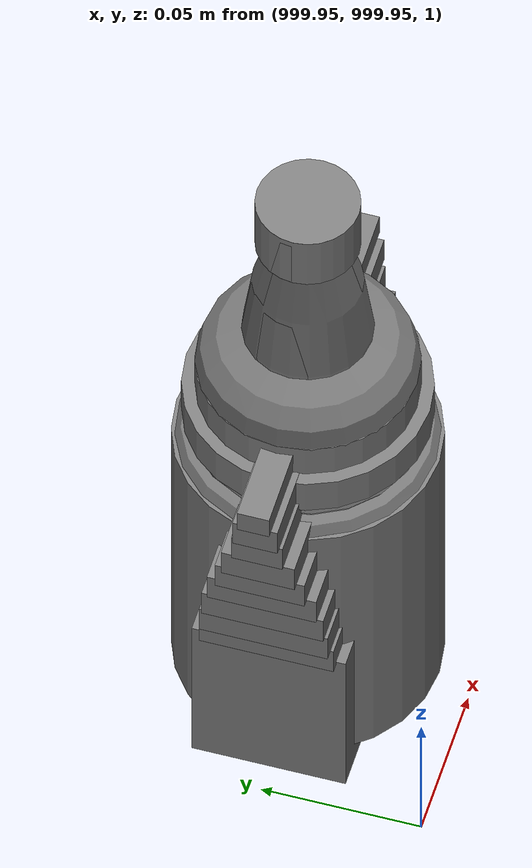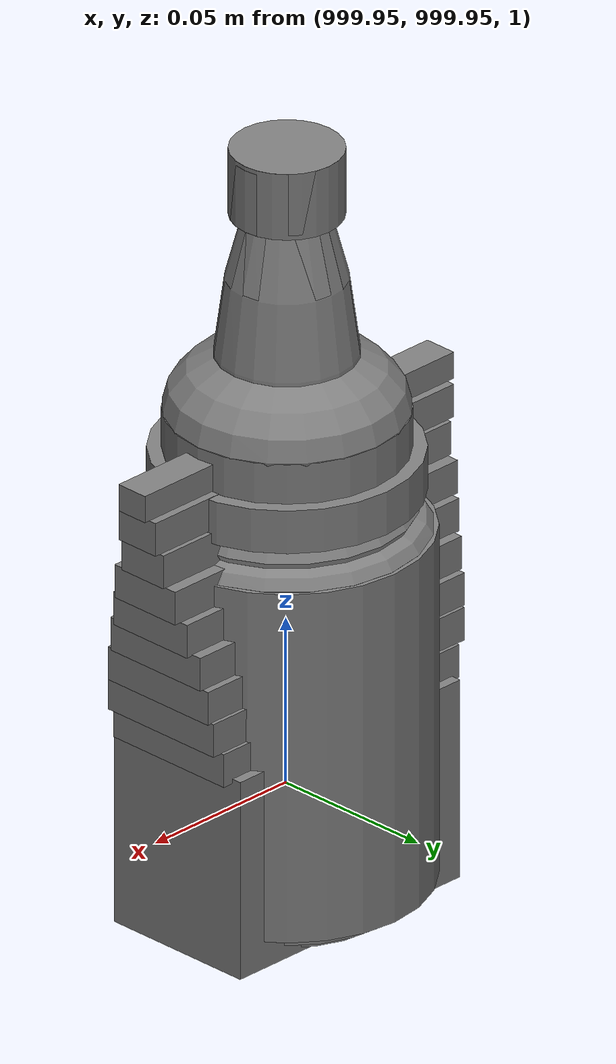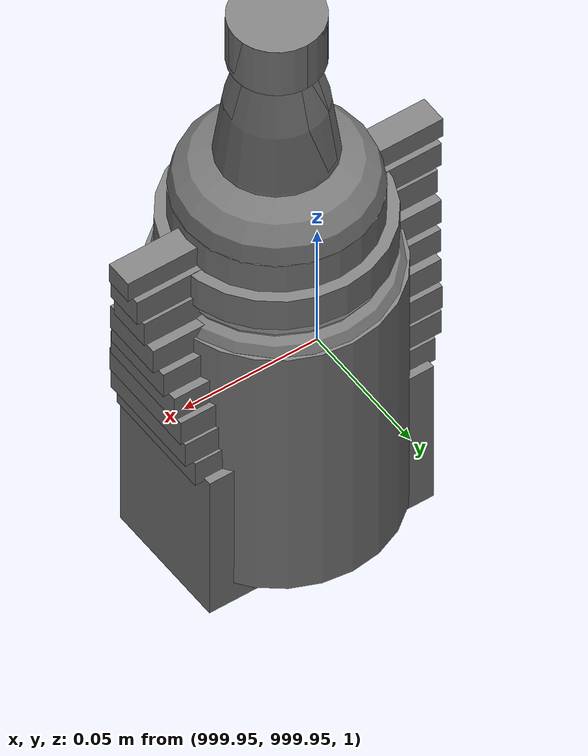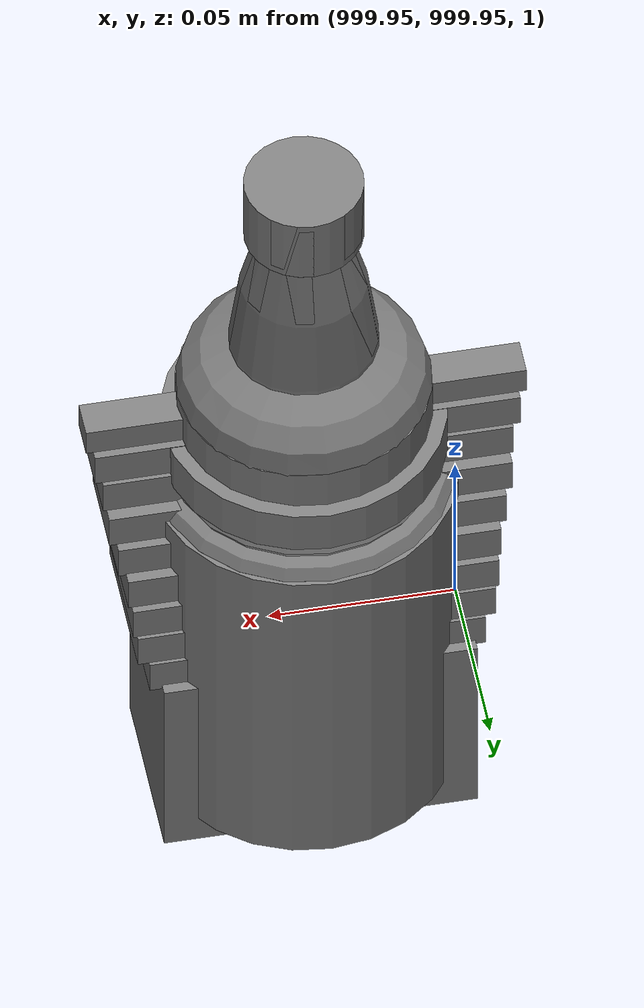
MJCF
<mujoco>
    <option gravity="0.000000000 0.000000000 -9.810000420" timestep="0.0166666" integrator="implicitfast" density="1.225" viscosity="1.8000001e-05" noslip_iterations="10" iterations="100" sdf_iterations="50">
        <flag multiccd="disable"/>
    </option>
    <size memory="1000M"/>
    <compiler coordinate="local"/>
    <worldbody>
        <light cutoff="30" pos="0 1 1" dir="0 -1 -2"/>
        <light cutoff="30" pos="0 -1 1" dir="0 1 -2"/>
        <body pos="-7.168000221 2.823999882 1.227496982" euler="-0.283413976 0.056829724 -0.133293271" name="openloong_gripper_2f85_fix_base_usda_Pos">
            <geom contype="1" conaffinity="1" density="1000" type="box" material="" rgba="0.500000000 0.500000000 0.500000000 1.000000000" solimp="0.899999976 0.949999988 0.001000000" friction="1.000000000 0.005000000 0.000100000" solref="0.020000000 1.000000000" margin="0" condim="3" group="0" pos="-0.002278805 0.074524641 -0.004134059" quat="0.315989345 0.948763072 -0.000000000 0.000000000" size="0.059999999 0.013000000 0.035000000" name="openloong_gripper_2f85_fix_base_usda_geom_679E4B48_1C00_4016_AAB6_4A6E57F3BDA9"/>
            <geom contype="1" conaffinity="1" density="1000" type="box" material="" rgba="0.500000000 0.500000000 0.500000000 1.000000000" solimp="0.899999976 0.949999988 0.001000000" friction="1.000000000 0.005000000 0.000100000" solref="0.020000000 1.000000000" margin="0" condim="3" group="0" pos="-0.002278805 0.078031301 0.008128285" quat="0.990447521 -0.137893379 -0.000000000 -0.000000000" size="0.059999999 0.010000000 0.035000000" name="openloong_gripper_2f85_fix_base_usda_geom_B2ABBB4A_C9DB_46A5_987D_1C065BC603EB"/>
            <geom contype="1" conaffinity="1" density="1000" type="box" material="" rgba="0.500000000 0.500000000 0.500000000 1.000000000" solimp="0.899999976 0.949999988 0.001000000" friction="1.000000000 0.005000000 0.000100000" solref="0.020000000 1.000000000" margin="0" condim="3" group="0" pos="-0.002278805 0.080785275 -0.002596974" quat="0.287325472 -0.957833409 0.000000000 -0.000000000" size="0.059999999 0.013000000 0.035000000" name="openloong_gripper_2f85_fix_base_usda_geom_0B85F711_6DD5_4B71_981D_B7E0A26C4982"/>
            <geom contype="1" conaffinity="1" density="1000" type="box" material="" rgba="0.500000000 0.500000000 0.500000000 1.000000000" solimp="0.899999976 0.949999988 0.001000000" friction="1.000000000 0.005000000 0.000100000" solref="0.020000000 1.000000000" margin="0" condim="3" group="0" pos="-0.002278805 -0.098804474 -0.020146966" quat="0.988851666 0.148906454 0.000000000 -0.000000000" size="0.059999999 0.022000000 0.020000000" name="openloong_gripper_2f85_fix_base_usda_geom_236BC340_8C3B_4F2E_98BB_C97BB2632356"/>
            <geom contype="1" conaffinity="1" density="1000" type="box" material="" rgba="0.500000000 0.500000000 0.500000000 1.000000000" solimp="0.899999976 0.949999988 0.001000000" friction="1.000000000 0.005000000 0.000100000" solref="0.020000000 1.000000000" margin="0" condim="3" group="0" pos="-0.002279282 0.019920111 0.012102962" quat="0.995421767 0.095583342 -0.000000000 -0.000000000" size="0.059999999 0.025000000 0.026000001" name="openloong_gripper_2f85_fix_base_usda_geom_43C6B574_6FD8_403A_8D3B_084E9A1547FA"/>
            <geom contype="1" conaffinity="1" density="1000" type="box" material="" rgba="0.500000000 0.500000000 0.500000000 1.000000000" solimp="0.899999976 0.949999988 0.001000000" friction="1.000000000 0.005000000 0.000100000" solref="0.020000000 1.000000000" margin="0" condim="3" group="0" pos="-0.002279282 0.005734444 -0.014276862" quat="0.999571741 -0.029275302 -0.000000000 -0.000000000" size="0.059999999 0.050000001 0.010000000" name="openloong_gripper_2f85_fix_base_usda_geom_88E7C595_AE8D_4518_B58A_D942BBC5D2A2"/>
            <geom contype="1" conaffinity="1" density="1000" type="box" material="" rgba="0.500000000 0.500000000 0.500000000 1.000000000" solimp="0.899999976 0.949999988 0.001000000" friction="1.000000000 0.005000000 0.000100000" solref="0.020000000 1.000000000" margin="0" condim="3" group="0" pos="-0.002278805 0.079460382 0.007771969" quat="0.922590554 -0.385781586 0.000000000 -0.000000000" size="0.059999999 0.010000000 0.035000000" name="openloong_gripper_2f85_fix_base_usda_geom_6C88EEEF_FB53_4D83_8A0F_72030CFBD746"/>
            <geom contype="1" conaffinity="1" density="1000" type="box" material="" rgba="0.500000000 0.500000000 0.500000000 1.000000000" solimp="0.899999976 0.949999988 0.001000000" friction="1.000000000 0.005000000 0.000100000" solref="0.020000000 1.000000000" margin="0" condim="3" group="0" pos="-0.002279282 0.081384182 -0.001320124" quat="0.590483785 -0.807049930 0.000000000 -0.000000000" size="0.059999999 0.013000000 0.035000000" name="openloong_gripper_2f85_fix_base_usda_geom_93F603DB_0B8E_42FC_9B0E_B1F8133BE0C6"/>
            <geom contype="1" conaffinity="1" density="1000" type="box" material="" rgba="0.500000000 0.500000000 0.500000000 1.000000000" solimp="0.899999976 0.949999988 0.001000000" friction="1.000000000 0.005000000 0.000100000" solref="0.020000000 1.000000000" margin="0" condim="3" group="0" pos="-0.002278805 -0.059297800 -0.007972836" quat="0.988851666 0.148906454 0.000000000 -0.000000000" size="0.059999999 0.020000000 0.022000000" name="openloong_gripper_2f85_fix_base_usda_geom_C59D6596_509D_48F0_859D_7C5CD10B40C3"/>
            <geom contype="1" conaffinity="1" density="1000" type="box" material="" rgba="0.500000000 0.500000000 0.500000000 1.000000000" solimp="0.899999976 0.949999988 0.001000000" friction="1.000000000 0.005000000 0.000100000" solref="0.020000000 1.000000000" margin="0" condim="3" group="0" pos="-0.002278805 0.076618671 -0.004656792" quat="0.004634961 0.999989629 -0.000000000 0.000000000" size="0.059999999 0.013000000 0.035000000" name="openloong_gripper_2f85_fix_base_usda_geom_150A9E53_DE3B_4F41_8D27_624238CC4614"/>
            <geom contype="1" conaffinity="1" density="1000" type="box" material="" rgba="0.500000000 0.500000000 0.500000000 1.000000000" solimp="0.899999976 0.949999988 0.001000000" friction="1.000000000 0.005000000 0.000100000" solref="0.020000000 1.000000000" margin="0" condim="3" group="0" pos="-0.002279282 -0.021952629 0.002960086" quat="0.991270423 0.131847665 -0.000000000 0.000000000" size="0.059999999 0.020000000 0.024000000" name="openloong_gripper_2f85_fix_base_usda_geom_8A044AF2_1C90_4B91_AB95_0C6B36609E7A"/>
            <geom contype="1" conaffinity="1" density="1000" type="box" material="" rgba="0.500000000 0.500000000 0.500000000 1.000000000" solimp="0.899999976 0.949999988 0.001000000" friction="1.000000000 0.005000000 0.000100000" solref="0.020000000 1.000000000" margin="0" condim="3" group="0" pos="-0.002278805 0.081418991 0.002587914" quat="0.803492308 -0.595315695 0.000000000 -0.000000000" size="0.059999999 0.013000000 0.035000000" name="openloong_gripper_2f85_fix_base_usda_geom_619D876F_40A7_4838_89DF_61AD4BE19A34"/>
            <geom contype="1" conaffinity="1" density="1000" type="box" material="" rgba="0.500000000 0.500000000 0.500000000 1.000000000" solimp="0.899999976 0.949999988 0.001000000" friction="1.000000000 0.005000000 0.000100000" solref="0.020000000 1.000000000" margin="0" condim="3" group="0" pos="-0.002278805 0.061115503 0.008545756" quat="0.999326169 0.036714450 0.000000000 -0.000000000" size="0.059999999 0.020000000 0.035000000" name="openloong_gripper_2f85_fix_base_usda_geom_B9D4465D_A697_40AA_B83D_DD283628ABB4"/>
            <freejoint name="openloong_gripper_2f85_fix_base_usda_pos_scan"/>
        </body>
        <body pos="-1.802151084 5.900734425 1.824306011" euler="94.163223267 47.184070587 53.674037933" mocap="true" name="spotlight3_SpotLight"/>
        <body pos="1000.000000000 1000.000000000 1.000000000" euler="0.000000000 0.000000000 0.000000000" name="openloong_gripper_2f85_fix_base_usda_salt">
            <geom contype="1" conaffinity="1" density="1000" type="box" material="" rgba="0.500000000 0.500000000 0.500000000 1.000000000" solimp="0.899999976 0.949999988 0.001000000" friction="1.000000000 0.005000000 0.000100000" solref="0.020000000 1.000000000" margin="0" condim="3" group="0" pos="0.000305176 0.000000000 0.084862232" quat="1.000000000 0.000000000 0.000000000 0.000000000" size="0.048999999 0.018999999 0.005000000" name="openloong_gripper_2f85_fix_base_usda_geom_ED0BE09F_C92C_4F4A_82FA_A44EF7A1A01D"/>
            <geom contype="1" conaffinity="1" density="1000" type="box" material="" rgba="0.500000000 0.500000000 0.500000000 1.000000000" solimp="0.899999976 0.949999988 0.001000000" friction="1.000000000 0.005000000 0.000100000" solref="0.020000000 1.000000000" margin="0" condim="3" group="0" pos="0.000305176 0.000000000 0.104564309" quat="1.000000000 0.000000000 0.000000000 0.000000000" size="0.052000001 0.014000000 0.005000000" name="openloong_gripper_2f85_fix_base_usda_geom_F880A74D_F94D_4DF9_956B_75F4CF74A333"/>
            <geom contype="1" conaffinity="1" density="1000" type="box" material="" rgba="0.500000000 0.500000000 0.500000000 1.000000000" solimp="0.899999976 0.949999988 0.001000000" friction="1.000000000 0.005000000 0.000100000" solref="0.020000000 1.000000000" margin="0" condim="3" group="0" pos="0.000305176 0.000000000 0.114487171" quat="1.000000000 0.000000000 0.000000000 0.000000000" size="0.054000001 0.011500000 0.005000000" name="openloong_gripper_2f85_fix_base_usda_geom_633247E3_B73F_4AA9_A48E_655855122585"/>
            <geom contype="1" conaffinity="1" density="1000" type="box" material="" rgba="0.500000000 0.500000000 0.500000000 1.000000000" solimp="0.899999976 0.949999988 0.001000000" friction="1.000000000 0.005000000 0.000100000" solref="0.020000000 1.000000000" margin="0" condim="3" group="0" pos="0.000305176 0.000000000 0.075103164" quat="1.000000000 0.000000000 0.000000000 0.000000000" size="0.048000000 0.020000000 0.005000000" name="openloong_gripper_2f85_fix_base_usda_geom_26990CDC_C4DA_4EA6_8FE7_A68CFB86956F"/>
            <geom contype="1" conaffinity="1" density="1000" type="box" material="" rgba="0.500000000 0.500000000 0.500000000 1.000000000" solimp="0.899999976 0.949999988 0.001000000" friction="1.000000000 0.005000000 0.000100000" solref="0.020000000 1.000000000" margin="0" condim="3" group="0" pos="0.000305176 0.000000000 0.134892464" quat="1.000000000 0.000000000 0.000000000 0.000000000" size="0.057000000 0.007000000 0.005000000" name="openloong_gripper_2f85_fix_base_usda_geom_71E22DE7_095A_4C5F_AEF8_D4AB70D7196F"/>
            <geom contype="1" conaffinity="1" density="1000" type="box" material="" rgba="0.500000000 0.500000000 0.500000000 1.000000000" solimp="0.899999976 0.949999988 0.001000000" friction="1.000000000 0.005000000 0.000100000" solref="0.020000000 1.000000000" margin="0" condim="3" group="0" pos="0.000305176 0.000000000 0.094920278" quat="1.000000000 0.000000000 0.000000000 0.000000000" size="0.050000001 0.017000001 0.005000000" name="openloong_gripper_2f85_fix_base_usda_geom_55BA2EBC_F964_4802_B058_3777955C765E"/>
            <geom contype="1" conaffinity="1" density="1000" type="box" material="" rgba="0.500000000 0.500000000 0.500000000 1.000000000" solimp="0.899999976 0.949999988 0.001000000" friction="1.000000000 0.005000000 0.000100000" solref="0.020000000 1.000000000" margin="0" condim="3" group="0" pos="0.000305176 0.000000000 0.065204859" quat="1.000000000 0.000000000 0.000000000 0.000000000" size="0.045000002 0.021000000 0.005000000" name="openloong_gripper_2f85_fix_base_usda_geom_7D822170_A67F_4AAE_BECF_7734E37F02A6"/>
            <geom contype="1" conaffinity="1" density="1000" type="box" material="" rgba="0.500000000 0.500000000 0.500000000 1.000000000" solimp="0.899999976 0.949999988 0.001000000" friction="1.000000000 0.005000000 0.000100000" solref="0.020000000 1.000000000" margin="0" condim="3" group="0" pos="0.000305176 0.000000000 0.144135714" quat="1.000000000 0.000000000 0.000000000 0.000000000" size="0.059000000 0.005000000 0.004000000" name="openloong_gripper_2f85_fix_base_usda_geom_77597BDD_305E_405F_BAB7_CB9096BB30E3"/>
            <geom contype="1" conaffinity="1" density="1000" type="box" material="" rgba="0.500000000 0.500000000 0.500000000 1.000000000" solimp="0.899999976 0.949999988 0.001000000" friction="1.000000000 0.005000000 0.000100000" solref="0.020000000 1.000000000" margin="0" condim="3" group="0" pos="0.000000000 0.000000000 0.031593561" quat="1.000000000 0.000000000 0.000000000 0.000000000" size="0.041999999 0.024000000 0.029999999" name="openloong_gripper_2f85_fix_base_usda_geom_60A44098_ECD1_41A5_9FF9_4992B5C31CAE"/>
            <geom contype="1" conaffinity="1" density="1000" type="box" material="" rgba="0.500000000 0.500000000 0.500000000 1.000000000" solimp="0.899999976 0.949999988 0.001000000" friction="1.000000000 0.005000000 0.000100000" solref="0.020000000 1.000000000" margin="0" condim="3" group="0" pos="0.000305176 0.000000000 0.124608755" quat="1.000000000 0.000000000 0.000000000 0.000000000" size="0.055000000 0.008000000 0.005000000" name="openloong_gripper_2f85_fix_base_usda_geom_BD77E02B_EB65_467D_B855_2213D8F8607D"/>
            <freejoint name="openloong_gripper_2f85_fix_base_usda_salt_joint"/>
            <site size="0.005000000 0.005000000 0.005000000" rgba="0.500000000 0.500000000 0.500000000 1.000000000" pos="0.000000000 0.000000000 0.000000000" quat="1.000000000 0.000000000 0.000000000 0.000000000" group="0" type="sphere" name="openloong_gripper_2f85_fix_base_usda_saltsite"/>
        </body>
        <body pos="1000.000000000 1000.000000000 1.000000000" euler="0.000000000 0.000000000 0.000000000" name="openloong_gripper_2f85_fix_base_usda_jar_01">
            <geom contype="1" conaffinity="1" density="1000" type="box" material="" rgba="0.500000000 0.500000000 0.500000000 1.000000000" solimp="0.899999976 0.949999988 0.001000000" friction="1.000000000 0.005000000 0.000100000" solref="0.020000000 1.000000000" margin="0" condim="3" group="0" pos="0.000000000 0.000000000 0.006158113" quat="1.000000000 0.000000000 0.000000000 0.000000000" size="0.020000000 0.020000000 0.005000000" name="openloong_gripper_2f85_fix_base_usda_geom_2506D72A_1B4B_4117_847F_2D00EDA06839"/>
            <geom contype="1" conaffinity="1" density="1000" type="cylinder" material="" rgba="0.500000000 0.500000000 0.500000000 1.000000000" solimp="0.899999976 0.949999988 0.001000000" friction="1.000000000 0.005000000 0.000100000" solref="0.020000000 1.000000000" margin="0" condim="3" group="0" pos="0.000000000 0.000000000 0.062744498" quat="1.000000000 0.000000000 0.000000000 0.000000000" size="0.041000001 0.052999999 1.000000000" name="openloong_gripper_2f85_fix_base_usda_geom_EDC95141_5296_447D_A0B5_9C4260E65841"/>
            <geom contype="1" conaffinity="1" density="1000" type="ellipsoid" material="" rgba="0.500000000 0.500000000 0.500000000 1.000000000" solimp="0.899999976 0.949999988 0.001000000" friction="1.000000000 0.005000000 0.000100000" solref="0.020000000 1.000000000" margin="0" condim="3" group="0" pos="0.000000000 0.000000000 0.122252703" quat="1.000000000 0.000000000 0.000000000 0.000000000" size="0.035999998 0.035999998 0.010000000" name="openloong_gripper_2f85_fix_base_usda_geom_F8406F1B_960A_4EE5_842E_2D5B09895DD0"/>
            <geom contype="1" conaffinity="1" density="1000" type="cylinder" material="" rgba="0.500000000 0.500000000 0.500000000 1.000000000" solimp="0.899999976 0.949999988 0.001000000" friction="1.000000000 0.005000000 0.000100000" solref="0.020000000 1.000000000" margin="0" condim="3" group="0" pos="0.000000000 0.000000000 0.015747190" quat="1.000000000 0.000000000 0.000000000 0.000000000" size="0.035000000 0.010000000 1.000000000" name="openloong_gripper_2f85_fix_base_usda_geom_72A5A673_5F79_461D_928B_75698BEF05E0"/>
            <geom contype="1" conaffinity="1" density="1000" type="ellipsoid" material="" rgba="0.500000000 0.500000000 0.500000000 1.000000000" solimp="0.899999976 0.949999988 0.001000000" friction="1.000000000 0.005000000 0.000100000" solref="0.020000000 1.000000000" margin="0" condim="3" group="0" pos="0.000000000 0.000000000 0.115815401" quat="1.000000000 0.000000000 0.000000000 0.000000000" size="0.039999999 0.039999999 0.010000000" name="openloong_gripper_2f85_fix_base_usda_geom_AC4CB7FE_C344_4270_9346_10A40CE65BD1"/>
            <geom contype="1" conaffinity="1" density="1000" type="cylinder" material="" rgba="0.500000000 0.500000000 0.500000000 1.000000000" solimp="0.899999976 0.949999988 0.001000000" friction="1.000000000 0.005000000 0.000100000" solref="0.020000000 1.000000000" margin="0" condim="3" group="0" pos="0.000000000 0.000000000 0.133183479" quat="1.000000000 0.000000000 0.000000000 0.000000000" size="0.037999999 0.006500000 1.000000000" name="openloong_gripper_2f85_fix_base_usda_geom_6A4B35D7_CDA6_4840_89B2_5F09F865B73C"/>
            <freejoint name="openloong_gripper_2f85_fix_base_usda_jar_01_joint"/>
            <site size="0.005000000 0.005000000 0.005000000" rgba="0.500000000 0.500000000 0.500000000 1.000000000" pos="0.000000000 0.000000000 0.000000000" quat="1.000000000 0.000000000 0.000000000 0.000000000" group="0" type="sphere" name="openloong_gripper_2f85_fix_base_usda_jar_01site"/>
        </body>
        <body pos="-2.227333546 6.075915813 1.814617753" euler="177.755249023 44.788581848 66.470176697" mocap="true" name="spotlight5_SpotLight"/>
        <body pos="1000.000000000 1000.000000000 1.000000000" euler="0.000000000 0.000000000 0.000000000" name="openloong_gripper_2f85_fix_base_usda_bottle_red">
            <geom contype="1" conaffinity="1" density="1000" type="ellipsoid" material="" rgba="0.500000000 0.500000000 0.500000000 1.000000000" solimp="0.899999976 0.949999988 0.001000000" friction="1.000000000 0.005000000 0.000100000" solref="0.020000000 1.000000000" margin="0" condim="3" group="0" pos="0.000000000 0.000000000 0.144284487" quat="1.000000000 0.000000000 0.000000000 0.000000000" size="0.021000000 0.021000000 0.079999998" name="openloong_gripper_2f85_fix_base_usda_geom_39C67E79_9B42_4ACA_980A_BC962587A965"/>
            <geom contype="1" conaffinity="1" density="1000" type="cylinder" material="" rgba="0.500000000 0.500000000 0.500000000 1.000000000" solimp="0.899999976 0.949999988 0.001000000" friction="1.000000000 0.005000000 0.000100000" solref="0.020000000 1.000000000" margin="0" condim="3" group="0" pos="0.000000000 0.000000000 0.220618963" quat="1.000000000 0.000000000 0.000000000 0.000000000" size="0.016000001 0.010000000 1.000000000" name="openloong_gripper_2f85_fix_base_usda_geom_02429412_452A_4681_B1D8_764E68E535BE"/>
            <geom contype="1" conaffinity="1" density="1000" type="ellipsoid" material="" rgba="0.500000000 0.500000000 0.500000000 1.000000000" solimp="0.899999976 0.949999988 0.001000000" friction="1.000000000 0.005000000 0.000100000" solref="0.020000000 1.000000000" margin="0" condim="3" group="0" pos="0.000000000 0.000000000 0.118945479" quat="1.000000000 0.000000000 0.000000000 0.000000000" size="0.030999999 0.030999999 0.029999999" name="openloong_gripper_2f85_fix_base_usda_geom_24C6D08E_E833_4628_9852_C9BD51D3CBFD"/>
            <geom contype="1" conaffinity="1" density="1000" type="box" material="" rgba="0.500000000 0.500000000 0.500000000 1.000000000" solimp="0.899999976 0.949999988 0.001000000" friction="1.000000000 0.005000000 0.000100000" solref="0.020000000 1.000000000" margin="0" condim="3" group="0" pos="0.000000000 0.000000000 0.002189159" quat="1.000000000 0.000000000 0.000000000 0.000000000" size="0.020000000 0.020000000 0.003000000" name="openloong_gripper_2f85_fix_base_usda_geom_C38A0E3C_E01B_42E2_899A_90DF3C76A6F2"/>
            <geom contype="1" conaffinity="1" density="1000" type="cylinder" material="" rgba="0.500000000 0.500000000 0.500000000 1.000000000" solimp="0.899999976 0.949999988 0.001000000" friction="1.000000000 0.005000000 0.000100000" solref="0.020000000 1.000000000" margin="0" condim="3" group="0" pos="0.000000000 -0.000366211 0.060884237" quat="1.000000000 0.000000000 0.000000000 0.000000000" size="0.030999999 0.057999998 1.000000000" name="openloong_gripper_2f85_fix_base_usda_geom_857A644C_A00B_46B4_9F01_1750A1347F10"/>
            <freejoint name="openloong_gripper_2f85_fix_base_usda_bottle_red_joint"/>
            <site size="0.005000000 0.005000000 0.005000000" rgba="0.500000000 0.500000000 0.500000000 1.000000000" pos="0.000000000 0.000000000 0.000000000" quat="0.999961913 0.008726535 0.000000000 0.000000000" group="0" type="sphere" name="openloong_gripper_2f85_fix_base_usda_bottle_redsite"/>
        </body>
        <body pos="1000.000000000 1000.000000000 1.000000000" euler="0.000000000 0.000000000 0.000000000" name="openloong_gripper_2f85_fix_base_usda_can">
            <geom contype="1" conaffinity="1" density="1000" type="cylinder" material="" rgba="0.500000000 0.500000000 0.500000000 1.000000000" solimp="0.899999976 0.949999988 0.001000000" friction="1.000000000 0.005000000 0.000100000" solref="0.020000000 1.000000000" margin="0" condim="3" group="0" pos="0.000000000 0.000000000 0.079676986" quat="1.000000000 0.000000000 0.000000000 0.000000000" size="0.034000002 0.071999997 1.000000000" name="openloong_gripper_2f85_fix_base_usda_geom_692E2FB3_4B61_448B_825A_178CDA8C8854"/>
            <geom contype="1" conaffinity="1" density="1000" type="ellipsoid" material="" rgba="0.500000000 0.500000000 0.500000000 1.000000000" solimp="0.899999976 0.949999988 0.001000000" friction="1.000000000 0.005000000 0.000100000" solref="0.020000000 1.000000000" margin="0" condim="3" group="0" pos="0.000000000 0.000000000 0.151854277" quat="1.000000000 0.000000000 0.000000000 0.000000000" size="0.034000002 0.034000002 0.020000000" name="openloong_gripper_2f85_fix_base_usda_geom_A7A62106_A0BC_4653_A6CF_508831991C75"/>
            <geom contype="1" conaffinity="1" density="1000" type="box" material="" rgba="0.500000000 0.500000000 0.500000000 1.000000000" solimp="0.899999976 0.949999988 0.001000000" friction="1.000000000 0.005000000 0.000100000" solref="0.020000000 1.000000000" margin="0" condim="3" group="0" pos="0.000000000 0.000000000 0.004777670" quat="1.000000000 0.000000000 0.000000000 0.000000000" size="0.020000000 0.020000000 0.005000000" name="openloong_gripper_2f85_fix_base_usda_geom_0AFF5B5F_EE3B_47E0_9174_04DDF53B12A3"/>
            <freejoint name="openloong_gripper_2f85_fix_base_usda_can_joint"/>
            <site size="0.005000000 0.005000000 0.005000000" rgba="0.500000000 0.500000000 0.500000000 1.000000000" pos="0.000000000 0.000000000 0.000000000" quat="1.000000000 0.000000000 0.000000000 0.000000000" group="0" type="sphere" name="openloong_gripper_2f85_fix_base_usda_cansite"/>
        </body>
        <body pos="1000.000000000 1000.000000000 1.000000000" euler="0.000000000 0.000000000 0.000000000" name="openloong_gripper_2f85_fix_base_usda_bottle_blue">
            <geom contype="1" conaffinity="1" density="1000" type="ellipsoid" material="" rgba="0.500000000 0.500000000 0.500000000 1.000000000" solimp="0.899999976 0.949999988 0.001000000" friction="1.000000000 0.005000000 0.000100000" solref="0.020000000 1.000000000" margin="0" condim="3" group="0" pos="0.000000000 0.000000000 0.118920922" quat="1.000000000 0.000000000 0.000000000 0.000000000" size="0.030999999 0.030999999 0.029999999" name="openloong_gripper_2f85_fix_base_usda_geom_2EC9D051_F922_4B5A_81D3_61DCA963C77E"/>
            <geom contype="1" conaffinity="1" density="1000" type="box" material="" rgba="0.500000000 0.500000000 0.500000000 1.000000000" solimp="0.899999976 0.949999988 0.001000000" friction="1.000000000 0.005000000 0.000100000" solref="0.020000000 1.000000000" margin="0" condim="3" group="0" pos="0.000000000 0.000000000 0.002164602" quat="1.000000000 0.000000000 0.000000000 0.000000000" size="0.020000000 0.020000000 0.003000000" name="openloong_gripper_2f85_fix_base_usda_geom_53FFD368_1EF0_4349_B14C_CDD3ADA74847"/>
            <geom contype="1" conaffinity="1" density="1000" type="cylinder" material="" rgba="0.500000000 0.500000000 0.500000000 1.000000000" solimp="0.899999976 0.949999988 0.001000000" friction="1.000000000 0.005000000 0.000100000" solref="0.020000000 1.000000000" margin="0" condim="3" group="0" pos="0.000000000 -0.000366211 0.060859680" quat="1.000000000 0.000000000 0.000000000 0.000000000" size="0.030999999 0.057999998 1.000000000" name="openloong_gripper_2f85_fix_base_usda_geom_9067A5EA_8EB6_43E2_8B6D_FEFF35249D76"/>
            <geom contype="1" conaffinity="1" density="1000" type="cylinder" material="" rgba="0.500000000 0.500000000 0.500000000 1.000000000" solimp="0.899999976 0.949999988 0.001000000" friction="1.000000000 0.005000000 0.000100000" solref="0.020000000 1.000000000" margin="0" condim="3" group="0" pos="0.000000000 0.000000000 0.220594406" quat="1.000000000 0.000000000 0.000000000 0.000000000" size="0.016000001 0.010000000 1.000000000" name="openloong_gripper_2f85_fix_base_usda_geom_68D1ED89_FD12_44E4_B61C_1495DA453C50"/>
            <geom contype="1" conaffinity="1" density="1000" type="ellipsoid" material="" rgba="0.500000000 0.500000000 0.500000000 1.000000000" solimp="0.899999976 0.949999988 0.001000000" friction="1.000000000 0.005000000 0.000100000" solref="0.020000000 1.000000000" margin="0" condim="3" group="0" pos="0.000000000 0.000000000 0.144259930" quat="1.000000000 0.000000000 0.000000000 0.000000000" size="0.021000000 0.021000000 0.079999998" name="openloong_gripper_2f85_fix_base_usda_geom_0F6A8417_1201_48DD_AECD_0D0918586950"/>
            <freejoint name="openloong_gripper_2f85_fix_base_usda_bottle_blue_joint"/>
            <site size="0.005000000 0.005000000 0.005000000" rgba="0.500000000 0.500000000 0.500000000 1.000000000" pos="0.000000000 0.000000000 0.000000000" quat="0.999961913 0.008726535 0.000000000 0.000000000" group="0" type="sphere" name="openloong_gripper_2f85_fix_base_usda_bottle_bluesite"/>
        </body>
        <body pos="-2.272745609 6.116803646 1.750830293" euler="-8.069385529 80.286651611 89.766311646" mocap="true" name="spotlight1_SpotLight"/>
        <body pos="0.000000000 0.000000000 0.000000000" euler="0.000000000 0.000000000 0.000000000" name="Interactive Objects_Interactive Objects"/>
        <body pos="0.000000000 0.000000000 0.000000000" euler="0.000000000 0.000000000 0.000000000" name=" Static Objects_ Static Objects">
            <geom contype="1" conaffinity="1" density="1000" type="box" material="" rgba="0.500000000 0.500000000 0.500000000 1.000000000" solimp="0.899999976 0.949999988 0.001000000" friction="1.000000000 0.005000000 0.000100000" solref="0.020000000 1.000000000" margin="0" condim="3" group="0" pos="-6.286010742 6.153595448 1.563861728" quat="0.707107067 0.000000000 0.000000000 0.707106471" size="0.529999971 3.134999990 0.025000000" name=" Static Objects_geom_EB97D6E5_F1C0_48A2_AE01_EAEA1E8FC9B5"/>
            <geom contype="1" conaffinity="1" density="1000" type="box" material="" rgba="0.500000000 0.500000000 0.500000000 1.000000000" solimp="0.899999976 0.949999988 0.001000000" friction="1.000000000 0.005000000 0.000100000" solref="0.020000000 1.000000000" margin="0" condim="3" group="0" pos="-3.101639986 6.150595188 1.018643856" quat="1.000000000 0.000000000 0.000000000 0.000000000" size="0.050000001 0.579999983 1.019999981" name=" Static Objects_geom_743D0A80_3D11_4F52_9AFD_03F6295939B4"/>
            <geom contype="1" conaffinity="1" density="1000" type="box" material="" rgba="0.500000000 0.500000000 0.500000000 1.000000000" solimp="0.899999976 0.949999988 0.001000000" friction="1.000000000 0.005000000 0.000100000" solref="0.020000000 1.000000000" margin="0" condim="3" group="0" pos="-2.825197220 6.153595448 1.563861728" quat="0.707107067 0.000000000 0.000000000 0.707106471" size="0.550000012 0.239999995 0.025000000" name=" Static Objects_geom_08173D39_9E4D_4889_A6B5_32080FC449BB"/>
            <geom contype="1" conaffinity="1" density="1000" type="box" material="" rgba="0.500000000 0.500000000 0.500000000 1.000000000" solimp="0.899999976 0.949999988 0.001000000" friction="1.000000000 0.005000000 0.000100000" solref="0.020000000 1.000000000" margin="0" condim="3" group="0" pos="-6.311686516 6.153595448 1.018643856" quat="0.707107067 0.000000000 0.000000000 0.707106471" size="0.050000001 3.150000095 1.019999981" name=" Static Objects_geom_B544218D_69D6_43FF_839C_244AABE0C08D"/>
            <geom contype="1" conaffinity="1" density="1000" type="box" material="" rgba="0.500000000 0.500000000 0.500000000 1.000000000" solimp="0.899999976 0.949999988 0.001000000" friction="1.000000000 0.005000000 0.000100000" solref="0.020000000 1.000000000" margin="0" condim="3" group="0" pos="-2.825197220 6.153595448 1.115278244" quat="0.707107067 0.000000000 0.000000000 0.707106471" size="0.550000012 0.239999995 0.025000000" name=" Static Objects_geom_F1014B70_E598_45E1_B051_26DCF6F52A0F"/>
            <geom contype="1" conaffinity="1" density="1000" type="box" material="" rgba="0.500000000 0.500000000 0.500000000 1.000000000" solimp="0.899999976 0.949999988 0.001000000" friction="1.000000000 0.005000000 0.000100000" solref="0.020000000 1.000000000" margin="0" condim="3" group="0" pos="-6.293097973 6.153595448 1.114443064" quat="0.707107067 0.000000000 0.000000000 0.707106471" size="0.529999971 3.134999990 0.025000000" name=" Static Objects_geom_C73D9499_F3B7_4551_9410_D072FCC1815A"/>
            <geom contype="1" conaffinity="1" density="1000" type="box" material="" rgba="0.500000000 0.500000000 0.500000000 1.000000000" solimp="0.899999976 0.949999988 0.001000000" friction="1.000000000 0.005000000 0.000100000" solref="0.020000000 1.000000000" margin="0" condim="3" group="0" pos="-2.825197220 6.153595448 0.629031777" quat="0.707107067 0.000000000 0.000000000 0.707106471" size="0.550000012 0.239999995 0.025000000" name=" Static Objects_geom_EF2646DA_CBDA_44CB_9EB4_6CD4228BA424"/>
            <geom contype="1" conaffinity="1" density="1000" type="box" material="" rgba="0.500000000 0.500000000 0.500000000 1.000000000" solimp="0.899999976 0.949999988 0.001000000" friction="1.000000000 0.005000000 0.000100000" solref="0.020000000 1.000000000" margin="0" condim="3" group="0" pos="-6.286010742 6.153595448 0.096129179" quat="0.707107067 0.000000000 0.000000000 0.707106471" size="0.529999971 3.134999990 0.098999999" name=" Static Objects_geom_86C57C9C_BD54_479C_9E45_40DFD109B066"/>
            <geom contype="1" conaffinity="1" density="1000" type="box" material="" rgba="0.500000000 0.500000000 0.500000000 1.000000000" solimp="0.899999976 0.949999988 0.001000000" friction="1.000000000 0.005000000 0.000100000" solref="0.020000000 1.000000000" margin="0" condim="3" group="0" pos="-2.825197220 6.153595448 0.097434282" quat="0.707107067 0.000000000 0.000000000 0.707106471" size="0.550000012 0.239999995 0.098999999" name=" Static Objects_geom_8614FCF3_967A_44AE_9402_9CB11E34BD33"/>
            <geom contype="1" conaffinity="1" density="1000" type="box" material="" rgba="0.500000000 0.500000000 0.500000000 1.000000000" solimp="0.899999976 0.949999988 0.001000000" friction="1.000000000 0.005000000 0.000100000" solref="0.020000000 1.000000000" margin="0" condim="3" group="0" pos="-6.286010742 6.153595448 0.629031777" quat="0.707107067 0.000000000 0.000000000 0.707106471" size="0.529999971 3.134999990 0.025000000" name=" Static Objects_geom_A393E1C1_0248_4759_A804_59C14BB2E6A4"/>
            <geom contype="1" conaffinity="1" density="1000" type="box" material="" rgba="0.500000000 0.500000000 0.500000000 1.000000000" solimp="0.899999976 0.949999988 0.001000000" friction="1.000000000 0.005000000 0.000100000" solref="0.020000000 1.000000000" margin="0" condim="3" group="0" pos="-6.000000000 20.159999847 2.000000000" quat="1.000000000 0.000000000 0.000000000 0.000000000" size="6.079999924 0.070000000 2.000000000" name=" Static Objects_geom_6EE991E5_CD70_45CF_B2F0_A512E7ACDF2C"/>
            <geom contype="1" conaffinity="1" density="1000" type="box" material="" rgba="0.500000000 0.500000000 0.500000000 1.000000000" solimp="0.899999976 0.949999988 0.001000000" friction="1.000000000 0.005000000 0.000100000" solref="0.020000000 1.000000000" margin="0" condim="3" group="0" pos="-6.000000000 0.035000000 2.000000000" quat="1.000000000 0.000000000 0.000000000 0.000000000" size="6.079999924 0.070000000 2.000000000" name=" Static Objects_geom_94B259C3_EBC7_4EF8_BBE7_3650A122BD26"/>
            <geom contype="1" conaffinity="1" density="1000" type="box" material="" rgba="0.500000000 0.500000000 0.500000000 1.000000000" solimp="0.899999976 0.949999988 0.001000000" friction="1.000000000 0.005000000 0.000100000" solref="0.020000000 1.000000000" margin="0" condim="3" group="0" pos="0.000000000 10.000000000 2.000000000" quat="1.000000000 0.000000000 0.000000000 0.000000000" size="0.070000000 10.500000000 2.000000000" name=" Static Objects_geom_629C8A16_3989_4F16_A2E9_C5405C7DF4A7"/>
            <geom contype="1" conaffinity="1" density="1000" type="box" material="" rgba="0.500000000 0.500000000 0.500000000 1.000000000" solimp="0.899999976 0.949999988 0.001000000" friction="1.000000000 0.005000000 0.000100000" solref="0.020000000 1.000000000" margin="0" condim="3" group="0" pos="-12.050000191 10.000000000 2.000000000" quat="1.000000000 0.000000000 0.000000000 0.000000000" size="0.070000000 10.500000000 2.000000000" name=" Static Objects_geom_FF96E462_6454_4FAD_87DC_28EC88B4921D"/>
            <geom contype="1" conaffinity="1" density="1000" type="plane" material="" rgba="0.500000000 0.500000000 0.500000000 1.000000000" solimp="0.899999976 0.949999988 0.001000000" friction="1.000000000 0.005000000 0.000100000" solref="0.020000000 1.000000000" margin="0" condim="3" group="0" pos="-6.000000000 10.399999619 0.000000000" quat="1.000000000 0.000000000 0.000000000 0.000000000" size="6.050000191 10.800000191 0.010000000" name=" Static Objects_geom_D7146828_B186_40A9_B0DA_D8B49049BE03"/>
            <geom contype="1" conaffinity="1" density="1000" type="box" material="" rgba="0.500000000 0.500000000 0.500000000 1.000000000" solimp="0.899999976 0.949999988 0.001000000" friction="1.000000000 0.005000000 0.000100000" solref="0.020000000 1.000000000" margin="0" condim="3" group="0" pos="-8.830721855 2.096410990 0.549305558" quat="1.000000000 0.000000000 0.000000000 0.000000000" size="0.280000001 0.430000007 0.550000012" name=" Static Objects_geom_E88C3770_EA09_4D91_8E17_74A397DBA714"/>
            <geom contype="1" conaffinity="1" density="1000" type="box" material="" rgba="0.500000000 0.500000000 0.500000000 1.000000000" solimp="0.899999976 0.949999988 0.001000000" friction="1.000000000 0.005000000 0.000100000" solref="0.020000000 1.000000000" margin="0" condim="3" group="0" pos="-6.460197449 2.937205315 0.548931718" quat="1.000000000 0.000000000 0.000000000 0.000000000" size="2.650000095 0.430000007 0.550000012" name=" Static Objects_geom_868471C6_165A_4A5C_BA4E_4357E60FDF2C"/>
            <geom contype="1" conaffinity="1" density="1000" type="box" material="" rgba="0.500000000 0.500000000 0.500000000 1.000000000" solimp="0.899999976 0.949999988 0.001000000" friction="1.000000000 0.005000000 0.000100000" solref="0.020000000 1.000000000" margin="0" condim="3" group="0" pos="-4.240264893 1.327049494 0.549888909" quat="1.000000000 0.000000000 0.000000000 0.000000000" size="0.430000007 1.200000048 0.550000012" name=" Static Objects_geom_58FF55DC_9939_4191_BD06_C4DBA8CD6D3A"/>
            <geom contype="1" conaffinity="1" density="1000" type="box" material="" rgba="0.500000000 0.500000000 0.500000000 1.000000000" solimp="0.899999976 0.949999988 0.001000000" friction="1.000000000 0.005000000 0.000100000" solref="0.020000000 1.000000000" margin="0" condim="3" group="0" pos="-7.408766270 3.088089943 1.776644945" quat="0.928051054 0.000000000 0.000000000 0.372453064" size="0.050000001 0.100000001 0.050000001" name=" Static Objects_geom_D7D0D715_EBA2_42D1_A370_A0E190107629"/>
            <geom contype="1" conaffinity="1" density="1000" type="box" material="" rgba="0.500000000 0.500000000 0.500000000 1.000000000" solimp="0.899999976 0.949999988 0.001000000" friction="1.000000000 0.005000000 0.000100000" solref="0.020000000 1.000000000" margin="0" condim="3" group="0" pos="-7.437745571 3.067511320 1.289965630" quat="1.000000000 0.000000000 0.000000000 0.000000000" size="0.029999999 0.020000000 0.020000000" name=" Static Objects_geom_F7D6FD9C_6BC0_4273_AF8D_F847C3FA435B"/>
            <geom contype="1" conaffinity="1" density="1000" type="box" material="" rgba="0.500000000 0.500000000 0.500000000 1.000000000" solimp="0.899999976 0.949999988 0.001000000" friction="1.000000000 0.005000000 0.000100000" solref="0.020000000 1.000000000" margin="0" condim="3" group="0" pos="-7.719123363 2.867671013 1.173410416" quat="1.000000000 0.000000000 0.000000000 0.000000000" size="0.250000000 0.250000000 0.079999998" name=" Static Objects_geom_A8D3BAE7_4A2B_481B_9CDF_0B453625DE3B"/>
            <geom contype="1" conaffinity="1" density="1000" type="box" material="" rgba="0.500000000 0.500000000 0.500000000 1.000000000" solimp="0.899999976 0.949999988 0.001000000" friction="1.000000000 0.005000000 0.000100000" solref="0.020000000 1.000000000" margin="0" condim="3" group="0" pos="-7.719123363 2.958004713 1.530241251" quat="1.000000000 0.000000000 0.000000000 0.000000000" size="0.250000000 0.159999996 0.280000001" name=" Static Objects_geom_CAE6BBD0_0384_4164_83C7_9E8B59D7EDA2"/>
            <geom contype="1" conaffinity="1" density="1000" type="cylinder" material="" rgba="0.500000000 0.500000000 0.500000000 1.000000000" solimp="0.899999976 0.949999988 0.001000000" friction="1.000000000 0.005000000 0.000100000" solref="0.020000000 1.000000000" margin="0" condim="3" group="0" pos="-7.427312374 3.069516420 1.502544641" quat="0.928051054 0.000000000 0.000000000 0.372453064" size="0.015000000 0.230000004 0.100000001" name=" Static Objects_geom_30548F05_FD05_46ED_BB6F_C5BE38A258D8"/>
            <geom contype="1" conaffinity="1" density="1000" type="box" material="" rgba="0.500000000 0.500000000 0.500000000 1.000000000" solimp="0.899999976 0.949999988 0.001000000" friction="1.000000000 0.005000000 0.000100000" solref="0.020000000 1.000000000" margin="0" condim="3" group="0" pos="-9.058088303 6.434794426 1.209077358" quat="1.000000000 0.000000000 0.000000000 0.000000000" size="0.250000000 0.100000001 0.070000000" name=" Static Objects_geom_54B1A6BB_8C2B_4A92_B0DC_40996BE91151"/>
            <geom contype="1" conaffinity="1" density="1000" type="box" material="" rgba="0.500000000 0.500000000 0.500000000 1.000000000" solimp="0.899999976 0.949999988 0.001000000" friction="1.000000000 0.005000000 0.000100000" solref="0.020000000 1.000000000" margin="0" condim="3" group="0" pos="-5.611940861 6.318420410 0.350975692" quat="1.000000000 0.000000000 0.000000000 0.000000000" size="0.699999988 0.100000001 0.150000006" name=" Static Objects_geom_B3E60600_7E82_4B6A_AF35_8DE96394DF81"/>
            <geom contype="1" conaffinity="1" density="1000" type="box" material="" rgba="0.500000000 0.500000000 0.500000000 1.000000000" solimp="0.899999976 0.949999988 0.001000000" friction="1.000000000 0.005000000 0.000100000" solref="0.020000000 1.000000000" margin="0" condim="3" group="0" pos="-9.237723351 6.464855671 1.209077358" quat="1.000000000 0.000000000 0.000000000 0.000000000" size="0.100000001 0.100000001 0.070000000" name=" Static Objects_geom_126AF7E6_041E_4656_A0C9_A2C4924D96B2"/>
            <geom contype="1" conaffinity="1" density="1000" type="box" material="" rgba="0.500000000 0.500000000 0.500000000 1.000000000" solimp="0.899999976 0.949999988 0.001000000" friction="1.000000000 0.005000000 0.000100000" solref="0.020000000 1.000000000" margin="0" condim="3" group="0" pos="-6.300771236 6.459744930 1.744376063" quat="1.000000000 0.000000000 0.000000000 0.000000000" size="3.000000000 0.200000003 0.150000006" name=" Static Objects_geom_F26BDC33_64E7_466C_9CC3_D9A03C2663B3"/>
            <geom contype="1" conaffinity="1" density="1000" type="box" material="" rgba="0.500000000 0.500000000 0.500000000 1.000000000" solimp="0.899999976 0.949999988 0.001000000" friction="1.000000000 0.005000000 0.000100000" solref="0.020000000 1.000000000" margin="0" condim="3" group="0" pos="-7.373087406 6.458900928 1.214329123" quat="1.000000000 0.000000000 0.000000000 0.000000000" size="0.250000000 0.200000003 0.075000003" name=" Static Objects_geom_2742E441_4E36_4C7B_B7F1_C82DBB617673"/>
            <geom contype="1" conaffinity="1" density="1000" type="box" material="" rgba="0.500000000 0.500000000 0.500000000 1.000000000" solimp="0.899999976 0.949999988 0.001000000" friction="1.000000000 0.005000000 0.000100000" solref="0.020000000 1.000000000" margin="0" condim="3" group="0" pos="-4.035642624 6.459744930 0.352518857" quat="1.000000000 0.000000000 0.000000000 0.000000000" size="0.800000012 0.200000003 0.150000006" name=" Static Objects_geom_7210DC5A_8149_4DE3_AE68_F600331E09AF"/>
            <geom contype="1" conaffinity="1" density="1000" type="box" material="" rgba="0.500000000 0.500000000 0.500000000 1.000000000" solimp="0.899999976 0.949999988 0.001000000" friction="1.000000000 0.005000000 0.000100000" solref="0.020000000 1.000000000" margin="0" condim="3" group="0" pos="-3.907610416 6.318625927 0.800981164" quat="1.000000000 0.000000000 0.000000000 0.000000000" size="0.500000000 0.100000001 0.150000006" name=" Static Objects_geom_65726DBD_53A8_430B_B7A4_1AA70EAD2F42"/>
            <geom contype="1" conaffinity="1" density="1000" type="box" material="" rgba="0.500000000 0.500000000 0.500000000 1.000000000" solimp="0.899999976 0.949999988 0.001000000" friction="1.000000000 0.005000000 0.000100000" solref="0.020000000 1.000000000" margin="0" condim="3" group="0" pos="-6.098561764 6.327973843 1.292199373" quat="1.000000000 0.000000000 0.000000000 0.000000000" size="0.500000000 0.100000001 0.150000006" name=" Static Objects_geom_A5B56B63_0716_4285_9D67_4F4F233D7D03"/>
            <geom contype="1" conaffinity="1" density="1000" type="box" material="" rgba="0.500000000 0.500000000 0.500000000 1.000000000" solimp="0.899999976 0.949999988 0.001000000" friction="1.000000000 0.005000000 0.000100000" solref="0.020000000 1.000000000" margin="0" condim="3" group="0" pos="-7.886891365 6.459744930 0.352518857" quat="1.000000000 0.000000000 0.000000000 0.000000000" size="1.500000000 0.200000003 0.150000006" name=" Static Objects_geom_9FA0089C_E065_4FBB_8143_1788A11DFC85"/>
            <geom contype="1" conaffinity="1" density="1000" type="box" material="" rgba="0.500000000 0.500000000 0.500000000 1.000000000" solimp="0.899999976 0.949999988 0.001000000" friction="1.000000000 0.005000000 0.000100000" solref="0.020000000 1.000000000" margin="0" condim="3" group="0" pos="-6.824534416 6.447464466 1.212718010" quat="1.000000000 0.000000000 0.000000000 0.000000000" size="0.100000001 0.100000001 0.075000003" name=" Static Objects_geom_F7CB12BC_5F92_4793_AB13_F7594B3BDB23"/>
            <geom contype="1" conaffinity="1" density="1000" type="box" material="" rgba="0.500000000 0.500000000 0.500000000 1.000000000" solimp="0.899999976 0.949999988 0.001000000" friction="1.000000000 0.005000000 0.000100000" solref="0.020000000 1.000000000" margin="0" condim="3" group="0" pos="-4.407354832 6.459744930 1.292199373" quat="1.000000000 0.000000000 0.000000000 0.000000000" size="1.240000010 0.200000003 0.150000006" name=" Static Objects_geom_06892CA0_8BC0_4CD4_82E3_9BA9871F1547"/>
            <geom contype="1" conaffinity="1" density="1000" type="box" material="" rgba="0.500000000 0.500000000 0.500000000 1.000000000" solimp="0.899999976 0.949999988 0.001000000" friction="1.000000000 0.005000000 0.000100000" solref="0.020000000 1.000000000" margin="0" condim="3" group="0" pos="-6.751636982 6.459744930 0.800981164" quat="1.000000000 0.000000000 0.000000000 0.000000000" size="2.200000048 0.200000003 0.150000006" name=" Static Objects_geom_D3B0FF46_ED34_4A5B_9738_1F65BBFE9466"/>
            <geom contype="1" conaffinity="1" density="1000" type="box" material="" rgba="0.500000000 0.500000000 0.500000000 1.000000000" solimp="0.899999976 0.949999988 0.001000000" friction="1.000000000 0.005000000 0.000100000" solref="0.020000000 1.000000000" margin="0" condim="3" group="0" pos="-6.924745083 6.362090111 1.214329123" quat="1.000000000 0.000000000 0.000000000 0.000000000" size="0.200000003 0.100000001 0.075000003" name=" Static Objects_geom_9683FC03_250E_426F_BBB3_94A3464D3058"/>
            <geom contype="1" conaffinity="1" density="1000" type="box" material="" rgba="0.500000000 0.500000000 0.500000000 1.000000000" solimp="0.899999976 0.949999988 0.001000000" friction="1.000000000 0.005000000 0.000100000" solref="0.020000000 1.000000000" margin="0" condim="3" group="0" pos="-8.844120979 6.464855671 1.209077358" quat="1.000000000 0.000000000 0.000000000 0.000000000" size="0.100000001 0.100000001 0.070000000" name=" Static Objects_geom_E5887643_BBEC_4281_B069_2A60282CBDC7"/>
            <geom contype="1" conaffinity="1" density="1000" type="box" material="" rgba="0.500000000 0.500000000 0.500000000 1.000000000" solimp="0.899999976 0.949999988 0.001000000" friction="1.000000000 0.005000000 0.000100000" solref="0.020000000 1.000000000" margin="0" condim="3" group="0" pos="-3.157672644 6.136868477 1.348373055" quat="1.000000000 0.000000000 0.000000000 0.000000000" size="0.200000003 0.519999981 0.300000012" name=" Static Objects_geom_C332E9E4_61D4_4DF0_9B31_3B885FA1F0E6"/>
        </body>
        <body pos="-6.332345009 2.779978037 1.034067392" euler="0.000000000 0.000000000 0.000000000" name="openloong_gripper_2f85_fix_base_usda_basket">
            <geom contype="1" conaffinity="1" density="100000" type="box" material="" rgba="0.500000000 0.500000000 0.500000000 1.000000000" solimp="0.899999976 0.949999988 0.001000000" friction="1.000000000 0.899999976 0.000100000" solref="0.020000000 1.000000000" margin="0" condim="3" group="0" pos="-0.039724827 -0.188568115 0.167089701" quat="0.997537494 0.070135131 0.000000000 0.000000000" size="0.150000006 0.006000000 0.108000003" name="openloong_gripper_2f85_fix_base_usda_geom_E28B2DA1_546B_4CF3_B39E_7EC4004768E1"/>
            <geom contype="1" conaffinity="1" density="100000" type="box" material="" rgba="0.500000000 0.500000000 0.500000000 1.000000000" solimp="0.899999976 0.949999988 0.001000000" friction="1.000000000 0.899999976 0.000100000" solref="0.020000000 1.000000000" margin="0" condim="3" group="0" pos="0.094372749 0.000000000 0.168361664" quat="0.706172049 0.036353335 0.036353379 0.706171215" size="0.200000003 0.006000000 0.108000003" name="openloong_gripper_2f85_fix_base_usda_geom_4998CF87_8BE9_4075_86A0_71EDBE266FE2"/>
            <geom contype="1" conaffinity="1" density="100000" type="box" material="" rgba="0.500000000 0.500000000 0.500000000 1.000000000" solimp="0.899999976 0.949999988 0.001000000" friction="1.000000000 0.899999976 0.000100000" solref="0.020000000 1.000000000" margin="0" condim="3" group="0" pos="-0.039724827 0.000000000 0.068126202" quat="1.000000000 0.000000000 0.000000000 0.000000000" size="0.129999995 0.174999997 0.006000000" name="openloong_gripper_2f85_fix_base_usda_geom_BF3C719B_46A8_49DA_A65A_3014D6367469"/>
            <geom contype="1" conaffinity="1" density="100000" type="box" material="" rgba="0.500000000 0.500000000 0.500000000 1.000000000" solimp="0.899999976 0.949999988 0.001000000" friction="1.000000000 0.899999976 0.000100000" solref="0.020000000 1.000000000" margin="0" condim="3" group="0" pos="-0.039724827 0.188377380 0.167089701" quat="0.997489929 -0.070808925 0.000000000 0.000000000" size="0.150000006 0.006000000 0.108000003" name="openloong_gripper_2f85_fix_base_usda_geom_BDD8C88F_174D_44C1_B4CD_590D2B7DCE02"/>
            <geom contype="1" conaffinity="1" density="100000" type="box" material="" rgba="0.500000000 0.500000000 0.500000000 1.000000000" solimp="0.899999976 0.949999988 0.001000000" friction="1.000000000 0.899999976 0.000100000" solref="0.020000000 1.000000000" margin="0" condim="3" group="0" pos="-0.172339439 0.000000000 0.168361664" quat="0.706172407 -0.036353018 -0.036353093 0.706170976" size="0.200000003 0.006000000 0.108000003" name="openloong_gripper_2f85_fix_base_usda_geom_D33DBAEF_71F6_406B_BD0B_3C3ADC6837C8"/>
            <freejoint name="openloong_gripper_2f85_fix_base_usda_basket_joint"/>
            <site size="0.005000000 0.005000000 0.005000000" rgba="0.500000000 0.500000000 0.500000000 1.000000000" pos="0.000000000 0.000000000 0.000000000" quat="1.000000000 0.000000000 0.000000000 0.000000000" group="0" type="sphere" name="openloong_gripper_2f85_fix_base_usda_basketsite"/>
        </body>
        <body pos="-3.510578632 3.403555870 -0.000000100" euler="0.000000000 0.000000000 40.200675964" name="openloong_gripper_2f85_fix_base_usda_PZ">
            <geom contype="1" conaffinity="1" density="1000" type="box" material="" rgba="0.500000000 0.500000000 0.500000000 1.000000000" solimp="0.899999976 0.949999988 0.001000000" friction="1.000000000 0.005000000 0.000100000" solref="0.020000000 1.000000000" margin="0" condim="3" group="0" pos="-0.047453165 0.056484699 0.373715430" quat="0.934750080 0.077914521 0.028795123 0.345459938" size="0.180000007 0.010000000 0.379999995" name="openloong_gripper_2f85_fix_base_usda_geom_BF2843AC_9018_4DA5_8623_8F31BAF26900"/>
            <geom contype="1" conaffinity="1" density="1000" type="box" material="" rgba="0.500000000 0.500000000 0.500000000 1.000000000" solimp="0.899999976 0.949999988 0.001000000" friction="1.000000000 0.005000000 0.000100000" solref="0.020000000 1.000000000" margin="0" condim="3" group="0" pos="0.047452450 -0.054376602 0.374072611" quat="0.934387863 -0.082143910 -0.030358355 0.345326364" size="0.180000007 0.010000000 0.379999995" name="openloong_gripper_2f85_fix_base_usda_geom_2BC1B8E2_3767_4A25_9E2A_572F34DBF2C8"/>
            <freejoint name="openloong_gripper_2f85_fix_base_usda_PZ"/>
        </body>
        <body pos="-2.436573029 6.404376507 0.137849092" euler="0.000000000 0.000000000 0.000000000" name="openloong_gripper_2f85_fix_base_usda_shoppingtrolley_01">
            <geom contype="1" conaffinity="1" density="1000" type="box" material="" rgba="0.500000000 0.500000000 0.500000000 1.000000000" solimp="0.899999976 0.949999988 0.001000000" friction="1.000000000 0.005000000 0.000100000" solref="0.020000000 1.000000000" margin="0" condim="3" group="0" pos="-0.107458733 0.238907143 0.911498845" quat="0.634576976 0.622505128 -0.330067992 -0.317575932" size="0.017999999 0.022499999 0.035999998" name="openloong_gripper_2f85_fix_base_usda_geom_9C0CCCB5_27DD_44EF_8C37_8157C60E751A"/>
            <geom contype="1" conaffinity="1" density="1000" type="box" material="" rgba="0.500000000 0.500000000 0.500000000 1.000000000" solimp="0.899999976 0.949999988 0.001000000" friction="1.000000000 0.005000000 0.000100000" solref="0.020000000 1.000000000" margin="0" condim="3" group="0" pos="-0.126757339 -0.182533979 0.598989725" quat="0.996607184 0.055331606 -0.059003651 -0.015205891" size="0.013499999 0.287999988 0.053999998" name="openloong_gripper_2f85_fix_base_usda_geom_58E6BA89_3A77_4216_8137_D9215C7D3A00"/>
            <geom contype="1" conaffinity="1" density="1000" type="box" material="" rgba="0.500000000 0.500000000 0.500000000 1.000000000" solimp="0.899999976 0.949999988 0.001000000" friction="1.000000000 0.005000000 0.000100000" solref="0.020000000 1.000000000" margin="0" condim="3" group="0" pos="-0.005004787 0.248085022 0.912686050" quat="1.000000000 0.000000000 0.000000000 0.000000000" size="0.107999995 0.022499999 0.022499999" name="openloong_gripper_2f85_fix_base_usda_geom_AE641E6A_DE8E_414E_91B4_5D2B70229FAD"/>
            <geom contype="1" conaffinity="1" density="1000" type="box" material="" rgba="0.500000000 0.500000000 0.500000000 1.000000000" solimp="0.899999976 0.949999988 0.001000000" friction="1.000000000 0.005000000 0.000100000" solref="0.020000000 1.000000000" margin="0" condim="3" group="0" pos="-0.169898406 -0.043119621 0.915120542" quat="0.687021017 0.726584017 -0.005590606 -0.006832919" size="0.017999999 0.022499999 0.089999996" name="openloong_gripper_2f85_fix_base_usda_geom_409510A7_339F_4E33_B65B_8F4BBCCDD2FB"/>
            <geom contype="1" conaffinity="1" density="1000" type="box" material="" rgba="0.500000000 0.500000000 0.500000000 1.000000000" solimp="0.899999976 0.949999988 0.001000000" friction="1.000000000 0.005000000 0.000100000" solref="0.020000000 1.000000000" margin="0" condim="3" group="0" pos="0.148195267 -0.199506566 0.782808602" quat="0.998808920 0.017156634 0.026950166 0.036880098" size="0.013499999 0.305999994 0.063000001" name="openloong_gripper_2f85_fix_base_usda_geom_FB28A707_BF5D_4C8A_A7DE_A33FC9AE14AB"/>
            <geom contype="1" conaffinity="1" density="1000" type="box" material="" rgba="0.500000000 0.500000000 0.500000000 1.000000000" solimp="0.899999976 0.949999988 0.001000000" friction="1.000000000 0.005000000 0.000100000" solref="0.020000000 1.000000000" margin="0" condim="3" group="0" pos="-0.142927840 -0.199506134 0.784674108" quat="0.998421252 0.016904408 -0.027109101 -0.046199299" size="0.013499999 0.305999994 0.063000001" name="openloong_gripper_2f85_fix_base_usda_geom_4981D126_819F_4F7B_B2D8_EA05A379E089"/>
            <geom contype="1" conaffinity="1" density="1000" type="box" material="" rgba="0.500000000 0.500000000 0.500000000 1.000000000" solimp="0.899999976 0.949999988 0.001000000" friction="1.000000000 0.005000000 0.000100000" solref="0.020000000 1.000000000" margin="0" condim="3" group="0" pos="-0.000004721 -0.174527690 0.560063601" quat="0.996704638 0.081116498 -0.000000004 0.000000000" size="0.126000002 0.287999988 0.009000000" name="openloong_gripper_2f85_fix_base_usda_geom_E2D3DF6B_91BB_4FB2_866D_F831CA31DFC2"/>
            <geom contype="1" conaffinity="1" density="1000" type="box" material="" rgba="0.500000000 0.500000000 0.500000000 1.000000000" solimp="0.899999976 0.949999988 0.001000000" friction="1.000000000 0.005000000 0.000100000" solref="0.020000000 1.000000000" margin="0" condim="3" group="0" pos="-0.160832763 0.103427693 0.910528183" quat="0.711469591 0.699786782 -0.048386075 -0.042050660" size="0.017999999 0.022499999 0.071999997" name="openloong_gripper_2f85_fix_base_usda_geom_DE6F28C7_D512_4688_9B04_F2E8E0C5EA0E"/>
            <geom contype="1" conaffinity="1" density="1000" type="box" material="" rgba="0.500000000 0.500000000 0.500000000 1.000000000" solimp="0.899999976 0.949999988 0.001000000" friction="1.000000000 0.005000000 0.000100000" solref="0.020000000 1.000000000" margin="0" condim="3" group="0" pos="-0.169898406 -0.178061336 0.864131629" quat="0.916343808 -0.400392294 -0.000000045 0.000000030" size="0.017999999 0.022499999 0.089999996" name="openloong_gripper_2f85_fix_base_usda_geom_62B4E068_E6EE_4858_85D7_3FF9DC739D46"/>
            <geom contype="1" conaffinity="1" density="1000" type="box" material="" rgba="0.500000000 0.500000000 0.500000000 1.000000000" solimp="0.899999976 0.949999988 0.001000000" friction="1.000000000 0.005000000 0.000100000" solref="0.020000000 1.000000000" margin="0" condim="3" group="0" pos="-0.000006008 -0.484932661 0.670727849" quat="0.997585475 0.069449045 -0.000000004 -0.000000089" size="0.179999992 0.013499999 0.170999989" name="openloong_gripper_2f85_fix_base_usda_geom_F3847A73_268E_4DC6_8103_025EFA68B0DF"/>
            <geom contype="1" conaffinity="1" density="1000" type="box" material="" rgba="0.500000000 0.500000000 0.500000000 1.000000000" solimp="0.899999976 0.949999988 0.001000000" friction="1.000000000 0.005000000 0.000100000" solref="0.020000000 1.000000000" margin="0" condim="3" group="0" pos="0.134013891 0.200098798 0.912192523" quat="0.692574680 -0.680924535 -0.166899428 0.169783980" size="0.017999999 0.022499999 0.035999998" name="openloong_gripper_2f85_fix_base_usda_geom_1BC9CBA6_23EB_4BAA_B402_5CD423BCD9C4"/>
            <geom contype="1" conaffinity="1" density="1000" type="box" material="" rgba="0.500000000 0.500000000 0.500000000 1.000000000" solimp="0.899999976 0.949999988 0.001000000" friction="1.000000000 0.005000000 0.000100000" solref="0.020000000 1.000000000" margin="0" condim="3" group="0" pos="0.141839072 -0.191051379 0.702451229" quat="0.997147262 0.056065105 0.045779929 0.021407485" size="0.013499999 0.287999988 0.053999998" name="openloong_gripper_2f85_fix_base_usda_geom_518EF9E2_5475_4B05_B8A3_0398C9FE88EA"/>
            <geom contype="1" conaffinity="1" density="1000" type="box" material="" rgba="0.500000000 0.500000000 0.500000000 1.000000000" solimp="0.899999976 0.949999988 0.001000000" friction="1.000000000 0.005000000 0.000100000" solref="0.020000000 1.000000000" margin="0" condim="3" group="0" pos="0.169898629 -0.178061336 0.864131629" quat="0.916343808 -0.400392294 -0.000000045 0.000000030" size="0.017999999 0.022499999 0.089999996" name="openloong_gripper_2f85_fix_base_usda_geom_53C9630C_CEF1_49C6_A6B3_E429556B1EEF"/>
            <geom contype="1" conaffinity="1" density="1000" type="box" material="" rgba="0.500000000 0.500000000 0.500000000 1.000000000" solimp="0.899999976 0.949999988 0.001000000" friction="1.000000000 0.005000000 0.000100000" solref="0.020000000 1.000000000" margin="0" condim="3" group="0" pos="-0.000005364 0.100332208 0.734785020" quat="0.999668717 0.025737956 -0.000000010 0.000000000" size="0.135000005 0.019800000 0.152999997" name="openloong_gripper_2f85_fix_base_usda_geom_8E7D322D_7B98_4435_9EAB_B44A28206AAA"/>
            <geom contype="1" conaffinity="1" density="1000" type="box" material="" rgba="0.500000000 0.500000000 0.500000000 1.000000000" solimp="0.899999976 0.949999988 0.001000000" friction="1.000000000 0.005000000 0.000100000" solref="0.020000000 1.000000000" margin="0" condim="3" group="0" pos="-0.012634277 -0.174527690 -0.088243507" quat="1.000000000 0.000000000 -0.000000004 0.000000000" size="0.135000005 0.287999988 0.044999998" name="openloong_gripper_2f85_fix_base_usda_geom_806221D9_DE74_4965_BA9A_3A066208F38C"/>
            <geom contype="1" conaffinity="1" density="1000" type="box" material="" rgba="0.500000000 0.500000000 0.500000000 1.000000000" solimp="0.899999976 0.949999988 0.001000000" friction="1.000000000 0.005000000 0.000100000" solref="0.020000000 1.000000000" margin="0" condim="3" group="0" pos="0.131482959 -0.182533979 0.598989725" quat="0.996607125 0.055331629 0.059003670 0.015205893" size="0.013499999 0.287999988 0.053999998" name="openloong_gripper_2f85_fix_base_usda_geom_60EB20D1_FC9F_4E04_A94A_5CB06AA965AD"/>
            <geom contype="1" conaffinity="1" density="1000" type="box" material="" rgba="0.500000000 0.500000000 0.500000000 1.000000000" solimp="0.899999976 0.949999988 0.001000000" friction="1.000000000 0.005000000 0.000100000" solref="0.020000000 1.000000000" margin="0" condim="3" group="0" pos="0.103667587 0.233050480 0.912927270" quat="0.634205043 -0.622199059 -0.324503720 0.324576139" size="0.017999999 0.022499999 0.035999998" name="openloong_gripper_2f85_fix_base_usda_geom_44F512C7_BEAA_4186_9E82_FD9F1BB4A7EF"/>
            <geom contype="1" conaffinity="1" density="1000" type="box" material="" rgba="0.500000000 0.500000000 0.500000000 1.000000000" solimp="0.899999976 0.949999988 0.001000000" friction="1.000000000 0.005000000 0.000100000" solref="0.020000000 1.000000000" margin="0" condim="3" group="0" pos="-0.134013891 0.200098798 0.912192523" quat="0.694057047 0.679413557 -0.172947660 -0.163618833" size="0.017999999 0.022499999 0.035999998" name="openloong_gripper_2f85_fix_base_usda_geom_A36901C7_97EC_4A74_8EF5_34AB54ED6CA4"/>
            <geom contype="1" conaffinity="1" density="1000" type="box" material="" rgba="0.500000000 0.500000000 0.500000000 1.000000000" solimp="0.899999976 0.949999988 0.001000000" friction="1.000000000 0.005000000 0.000100000" solref="0.020000000 1.000000000" margin="0" condim="3" group="0" pos="-0.135714188 -0.191051379 0.694841146" quat="0.997147322 0.056064609 -0.045779683 -0.021407485" size="0.013499999 0.287999988 0.053999998" name="openloong_gripper_2f85_fix_base_usda_geom_B7A82105_09B7_47A6_8CE5_E450B2B18E14"/>
            <geom contype="1" conaffinity="1" density="1000" type="box" material="" rgba="0.500000000 0.500000000 0.500000000 1.000000000" solimp="0.899999976 0.949999988 0.001000000" friction="1.000000000 0.005000000 0.000100000" solref="0.020000000 1.000000000" margin="0" condim="3" group="0" pos="0.169898629 -0.043119621 0.915120542" quat="0.687029123 -0.726576388 -0.006509603 0.005963952" size="0.017999999 0.022499999 0.089999996" name="openloong_gripper_2f85_fix_base_usda_geom_D80A044E_8FD6_4445_8F5D_268651243047"/>
            <geom contype="1" conaffinity="1" density="1000" type="box" material="" rgba="0.500000000 0.500000000 0.500000000 1.000000000" solimp="0.899999976 0.949999988 0.001000000" friction="1.000000000 0.005000000 0.000100000" solref="0.020000000 1.000000000" margin="0" condim="3" group="0" pos="0.160832971 0.103427693 0.910528183" quat="0.711112797 -0.700149298 -0.042821646 0.047705106" size="0.017999999 0.022499999 0.071999997" name="openloong_gripper_2f85_fix_base_usda_geom_CCAA1822_2EE7_4078_AFF3_906A7D73B1C1"/>
            <freejoint name="openloong_gripper_2f85_fix_base_usda_shoppingtrolley_01_joint"/>
            <site size="0.005000000 0.005000000 0.005000000" rgba="0.500000000 0.500000000 0.500000000 1.000000000" pos="0.000000000 0.000000000 0.000000000" quat="1.000000000 0.000000000 0.000000000 0.000000000" group="0" type="sphere" name="openloong_gripper_2f85_fix_base_usda_shoppingtrolley_01"/>
        </body>
        <body pos="-2.162922621 6.180304527 -0.123990871" euler="0.000000000 0.000000000 180.000000000" mocap="true" name="openloong_gripper_2f85_fix_base_usda_leftHandMocap"/>
        <body pos="-2.162922621 6.180304527 -0.123990871" euler="0.000000000 0.000000000 180.000000000" mocap="true" name="openloong_gripper_2f85_fix_base_usda_rightHandMocap"/>
        <body pos="-2.162922621 6.180304527 1.076009154" euler="0.000000000 0.000000000 180.000000000" name="openloong_gripper_2f85_fix_base_usda_base_link">
            <geom contype="1" conaffinity="1" density="1000" type="mesh" material="" rgba="0.783999979 0.783999979 0.783999979 1.000000000" solimp="0.899999976 0.949999988 0.001000000" friction="1.000000000 0.005000000 0.000100000" solref="0.020000000 1.000000000" margin="0" condim="3" group="3" mesh="base_link" pos="0.000000000 0.000000000 0.000000000" quat="1.000000000 0.000000000 0.000000000 0.000000000" size="1.000000000 1.000000000 1.000000000" name="openloong_gripper_2f85_fix_base_usda__geom_7_3C7F301C_F377_46B3_9C5A_F18CCB837B1A"/>
            <site size="0.005000000 0.005000000 0.005000000" rgba="0.500000000 0.500000000 0.500000000 1.000000000" pos="0.000000000 0.000000000 0.000000000" quat="1.000000000 0.000000000 0.000000000 0.000000000" group="0" type="sphere" name="openloong_gripper_2f85_fix_base_usda_imu"/>
            <inertial mass="22.447001" pos="-0.005664100 -0.001336700 0.238289997" diaginertia="0.374352545 0.277180195 0.220617250" quat="0.999247074 0.035235517 -0.015086859 0.006023135"/>
            <body pos="0.000000000 0.000000000 0.300000072" euler="0.000000000 0.000000000 0.000000000" name="openloong_gripper_2f85_fix_base_usda_dummy_body">
                <geom contype="1" conaffinity="1" density="1000" type="sphere" material="" rgba="0.783999979 0.783999979 0.783999979 1.000000000" solimp="0.899999976 0.949999988 0.001000000" friction="1.000000000 0.005000000 0.000100000" solref="0.020000000 1.000000000" margin="0" condim="3" group="3" pos="0.000000000 0.000000000 0.000000000" quat="1.000000000 0.000000000 0.000000000 0.000000000" size="0.010000000 0.000000000 0.000000000" name="openloong_gripper_2f85_fix_base_usda__geom_8_FC2922B9_0C8E_4F62_860E_54A35647E2DB"/>
                <joint armature="0.0099999998" stiffness="0" damping="0.1" axis="0.000000 0.000000 1.000000" type="hinge" name="openloong_gripper_2f85_fix_base_usda_dummy_joint"/>
                <site size="0.010000000 0.005000000 0.005000000" rgba="0.500000000 0.500000000 0.500000000 1.000000000" pos="0.000000000 0.000000000 0.000000000" quat="1.000000000 0.000000000 0.000000000 0.000000000" group="3" type="sphere" name="openloong_gripper_2f85_fix_base_usda_dummy_site"/>
            </body>
            <body pos="0.009000063 0.000000000 0.406399965" euler="0.000000000 0.000000000 0.000000000" name="openloong_gripper_2f85_fix_base_usda_Link_head_yaw">
                <geom contype="1" conaffinity="1" density="1000" type="mesh" material="" rgba="0.783999979 0.783999979 0.783999979 1.000000000" solimp="0.899999976 0.949999988 0.001000000" friction="1.000000000 0.005000000 0.000100000" solref="0.020000000 1.000000000" margin="0" condim="3" group="3" mesh="Link_head_yaw" pos="0.000000000 0.000000000 0.000000000" quat="1.000000000 0.000000000 0.000000000 0.000000000" size="1.000000000 1.000000000 1.000000000" name="openloong_gripper_2f85_fix_base_usda__geom_10_8DEE5D47_72DD_442C_BED5_FB4CAB8F5A87"/>
                <inertial mass="0.84249002" pos="0.000000000 -0.002081400 0.044801001" diaginertia="0.000700588 0.000629000 0.000553812" quat="0.706933022 -0.015675601 0.015677100 0.706933022"/>
                <body pos="0.000000000 -0.034599781 0.048499942" euler="0.000000000 0.000000000 0.000000000" name="openloong_gripper_2f85_fix_base_usda_Link_head_pitch">
                    <geom contype="1" conaffinity="1" density="1000" type="mesh" material="" rgba="0.783999979 0.783999979 0.783999979 1.000000000" solimp="0.899999976 0.949999988 0.001000000" friction="1.000000000 0.005000000 0.000100000" solref="0.020000000 1.000000000" margin="0" condim="3" group="3" mesh="Link_head_pitch" pos="0.000000000 0.000000000 0.000000000" quat="1.000000000 0.000000000 0.000000000 0.000000000" size="1.000000000 1.000000000 1.000000000" name="openloong_gripper_2f85_fix_base_usda__geom_12_6745CA65_5A41_4841_AF98_967F4B3FC8B4"/>
                    <inertial mass="1.3943" pos="0.020569000 0.033004001 0.125000000" diaginertia="0.006381400 0.006289940 0.004481460" quat="0.973390222 0.008406822 0.228157058 0.019624906"/>
                    <body pos="0.000000000 0.030000210 0.000000000" euler="0.000000000 0.000000000 0.000000000" name="openloong_gripper_2f85_fix_base_usda_neck_center_body">
                        <site size="0.010000000 0.005000000 0.005000000" rgba="0.500000000 0.500000000 0.500000000 1.000000000" pos="0.000000000 0.000000000 0.000000000" quat="1.000000000 0.000000000 0.000000000 0.000000000" group="3" type="sphere" name="openloong_gripper_2f85_fix_base_usda_neck_center_site"/>
                        <body pos="0.019999981 0.000000000 0.149999976" euler="-0.000002229 39.998176575 -90.000205994" name="openloong_gripper_2f85_fix_base_usda_camera_head">
                            <site size="0.010000000 0.005000000 0.005000000" rgba="0.500000000 0.500000000 0.500000000 1.000000000" pos="0.000000000 0.000000000 0.000000000" quat="1.000000000 0.000000000 0.000000000 0.000000000" group="3" type="sphere" name="openloong_gripper_2f85_fix_base_usda_camera_head_site"/>
                        </body>
                    </body>
                </body>
            </body>
            <body pos="0.003999949 -0.161600113 0.392199993" euler="0.000000000 0.000000000 0.000000000" name="openloong_gripper_2f85_fix_base_usda_Link_arm_r_01">
                <geom contype="1" conaffinity="1" density="1000" type="mesh" material="" rgba="0.783999979 0.783999979 0.783999979 1.000000000" solimp="0.899999976 0.949999988 0.001000000" friction="1.000000000 0.005000000 0.000100000" solref="0.020000000 1.000000000" margin="0" condim="3" group="3" mesh="Link_arm_r_01" pos="0.000000000 0.000000000 0.000000000" quat="1.000000000 0.000000000 0.000000000 0.000000000" size="1.000000000 1.000000000 1.000000000" name="openloong_gripper_2f85_fix_base_usda__geom_14_C7BE312A_AAA8_4AD9_8BBF_56E5199F9BEE"/>
                <joint armature="0.0099999998" stiffness="0" damping="1" axis="0.000000 -1.000000 0.000000" limited="true" range="-170.000015259 170.000015259" type="hinge" name="openloong_gripper_2f85_fix_base_usda_J_arm_r_01"/>
                <inertial mass="0.75641" pos="0.004494600 -0.038293999 -0.000001874" diaginertia="0.000842990 0.000803050 0.000587120" quat="-0.000163502 0.707098067 0.000812463 0.707115054"/>
                <body pos="-0.042000055 -0.040999889 0.000000000" euler="0.000000000 0.000000000 0.000000000" name="openloong_gripper_2f85_fix_base_usda_Link_arm_r_02">
                    <geom contype="1" conaffinity="1" density="1000" type="mesh" material="" rgba="0.783999979 0.783999979 0.783999979 1.000000000" solimp="0.899999976 0.949999988 0.001000000" friction="1.000000000 0.005000000 0.000100000" solref="0.020000000 1.000000000" margin="0" condim="3" group="3" mesh="Link_arm_r_02" pos="0.000000000 0.000000000 0.000000000" quat="1.000000000 0.000000000 0.000000000 0.000000000" size="1.000000000 1.000000000 1.000000000" name="openloong_gripper_2f85_fix_base_usda__geom_16_DAD4F0FC_EF92_4E9B_8EB9_F43407A306F7"/>
                    <joint armature="0.0099999998" stiffness="0" damping="1" axis="-1.000000 0.000000 0.000000" limited="true" range="-105.000244141 105.000244141" type="hinge" name="openloong_gripper_2f85_fix_base_usda_J_arm_r_02"/>
                    <inertial mass="0.98500001" pos="0.041999999 -0.067430697 0.000000000" diaginertia="0.002262690 0.001730990 0.001154020" quat="0.500000000 0.500000000 -0.500000000 0.500000000"/>
                    <body pos="0.042000055 -0.122600079 0.000000000" euler="0.000000000 0.000000000 0.000000000" name="openloong_gripper_2f85_fix_base_usda_Link_arm_r_03">
                        <geom contype="1" conaffinity="1" density="1000" type="mesh" material="" rgba="0.783999979 0.783999979 0.783999979 1.000000000" solimp="0.899999976 0.949999988 0.001000000" friction="1.000000000 0.005000000 0.000100000" solref="0.020000000 1.000000000" margin="0" condim="3" group="3" mesh="Link_arm_r_03" pos="0.000000000 0.000000000 0.000000000" quat="1.000000000 0.000000000 0.000000000 0.000000000" size="1.000000000 1.000000000 1.000000000" name="openloong_gripper_2f85_fix_base_usda__geom_18_12DC1368_AF8C_4599_8232_0DBDFC912258"/>
                        <joint armature="0.0099999998" stiffness="0" damping="1" axis="0.000000 -1.000000 0.000000" limited="true" range="-170.000015259 170.000015259" type="hinge" name="openloong_gripper_2f85_fix_base_usda_J_arm_r_03"/>
                        <inertial mass="0.95899999" pos="-0.001413580 -0.164663002 0.020757901" diaginertia="0.002101340 0.002064590 0.000754802" quat="0.560480952 0.454391927 -0.443732947 0.531497955"/>
                        <body pos="0.035300016 -0.177400112 0.024000049" euler="0.000000000 0.000000000 0.000000000" name="openloong_gripper_2f85_fix_base_usda_Link_arm_r_04">
                            <geom contype="1" conaffinity="1" density="1000" type="mesh" material="" rgba="0.783999979 0.783999979 0.783999979 1.000000000" solimp="0.899999976 0.949999988 0.001000000" friction="1.000000000 0.005000000 0.000100000" solref="0.020000000 1.000000000" margin="0" condim="3" group="3" mesh="Link_arm_r_04" pos="0.000000000 0.000000000 0.000000000" quat="1.000000000 0.000000000 0.000000000 0.000000000" size="1.000000000 1.000000000 1.000000000" name="openloong_gripper_2f85_fix_base_usda__geom_20_6FF4D462_8536_474B_8993_0AC55C7AE3E2"/>
                            <joint armature="0.0099999998" stiffness="0" damping="1" axis="-1.000000 0.000000 0.000000" limited="true" range="0.000000000 170.000015259" type="hinge" name="openloong_gripper_2f85_fix_base_usda_J_arm_r_04"/>
                            <inertial mass="0.60000002" pos="-0.038727000 -0.060766999 -0.021003000" diaginertia="0.001092610 0.000712422 0.000645102" quat="0.327701002 0.632602990 -0.467366993 0.523443997"/>
                            <body pos="-0.035300016 -0.103499889 -0.024000049" euler="0.000000000 0.000000000 0.000000000" name="openloong_gripper_2f85_fix_base_usda_Link_arm_r_05">
                                <geom contype="1" conaffinity="1" density="1000" type="mesh" material="" rgba="0.783999979 0.783999979 0.783999979 1.000000000" solimp="0.899999976 0.949999988 0.001000000" friction="1.000000000 0.005000000 0.000100000" solref="0.020000000 1.000000000" margin="0" condim="3" group="3" mesh="Link_arm_r_05" pos="0.000000000 0.000000000 0.000000000" quat="1.000000000 0.000000000 0.000000000 0.000000000" size="1.000000000 1.000000000 1.000000000" name="openloong_gripper_2f85_fix_base_usda__geom_22_07971CE1_28E9_48A6_9293_ADE963CBB558"/>
                                <joint armature="0.0099999998" stiffness="0" damping="1" axis="0.000000 -1.000000 0.000000" limited="true" range="-170.000015259 170.000015259" type="hinge" name="openloong_gripper_2f85_fix_base_usda_J_arm_r_05"/>
                                <inertial mass="0.68976003" pos="0.000032712 -0.068658002 -0.000111780" diaginertia="0.002522510 0.002411100 0.000448695" quat="0.707660973 0.706543028 -0.002603360 0.002470550"/>
                                <body pos="-0.026499987 -0.196499825 0.000000000" euler="0.000000000 0.000000000 0.000000000" name="openloong_gripper_2f85_fix_base_usda_Link_arm_r_06">
                                    <geom contype="1" conaffinity="1" density="1000" type="mesh" material="" rgba="0.783999979 0.783999979 0.783999979 1.000000000" solimp="0.899999976 0.949999988 0.001000000" friction="1.000000000 0.005000000 0.000100000" solref="0.020000000 1.000000000" margin="0" condim="3" group="3" mesh="Link_arm_r_06" pos="0.000000000 0.000000000 0.000000000" quat="1.000000000 0.000000000 0.000000000 0.000000000" size="1.000000000 1.000000000 1.000000000" name="openloong_gripper_2f85_fix_base_usda__geom_24_3CBCA06E_F26E_4DBD_B550_A427F456CB1D"/>
                                    <joint armature="0.0099999998" stiffness="0" damping="1" axis="1.000000 0.000000 0.000000" limited="true" range="-105.000244141 105.000244141" type="hinge" name="openloong_gripper_2f85_fix_base_usda_J_arm_r_06"/>
                                    <inertial mass="0.28" pos="0.026078001 -0.000000896 0.001663700" diaginertia="0.000156930 0.000145601 0.000104979" quat="0.707080841 0.001851080 0.001883810 0.707127810"/>
                                    <body pos="0.026499987 0.000000000 0.031800032" euler="0.000000000 0.000000000 0.000000000" name="openloong_gripper_2f85_fix_base_usda_Link_arm_r_07">
                                        <geom contype="1" conaffinity="1" density="1000" type="mesh" material="" rgba="0.783999979 0.783999979 0.783999979 1.000000000" solimp="0.899999976 0.949999988 0.001000000" friction="1.000000000 0.005000000 0.000100000" solref="0.020000000 1.000000000" margin="0" condim="3" group="3" mesh="Link_arm_r_07" pos="0.000000000 0.000000000 0.000000000" quat="1.000000000 0.000000000 0.000000000 0.000000000" size="1.000000000 1.000000000 1.000000000" name="openloong_gripper_2f85_fix_base_usda__geom_26_3B2B73B7_7F13_4250_A162_83BDCE4FDE26"/>
                                        <joint armature="0.0099999998" stiffness="0" damping="1" axis="0.000000 0.000000 1.000000" limited="true" range="-60.000133514 60.000133514" type="hinge" name="openloong_gripper_2f85_fix_base_usda_J_arm_r_07"/>
                                        <inertial mass="0.61353999" pos="-0.007859000 -0.158170000 -0.027736001" diaginertia="0.003037610 0.002570910 0.000729379" quat="0.427542925 0.443532884 -0.553093910 0.560867906"/>
                                        <body pos="0.000000000 0.287000179 -0.269999981" euler="150.000350952 0.000000000 0.000000000" name="openloong_gripper_2f85_fix_base_usda_camera_wrist_r">
                                            <site size="0.010000000 0.005000000 0.005000000" rgba="0.500000000 0.500000000 0.500000000 1.000000000" pos="0.000000000 0.000000000 0.000000000" quat="1.000000000 0.000000000 0.000000000 0.000000000" group="3" type="sphere" name="openloong_gripper_2f85_fix_base_usda_camera_wrist_r_site"/>
                                        </body>
                                        <body pos="0.000000000 -0.219999790 -0.032999992" euler="0.000000000 0.000000000 179.999969482" name="openloong_gripper_2f85_fix_base_usda_ee_center_body_r">
                                            <site size="0.010000000 0.005000000 0.005000000" rgba="0.500000000 0.500000000 0.500000000 1.000000000" pos="0.000000000 0.000000000 0.000000000" quat="1.000000000 0.000000000 0.000000000 0.000000000" group="3" type="sphere" name="openloong_gripper_2f85_fix_base_usda_ee_center_site_r"/>
                                        </body>
                                        <body pos="0.000000000 -0.065999985 -0.031000018" euler="89.999984741 0.000000000 180.000000000" name="openloong_gripper_2f85_fix_base_usda_zbr_base_link">
                                            <geom contype="1" conaffinity="1" density="1000" type="mesh" material="" rgba="0.783999979 0.783999979 0.783999979 1.000000000" solimp="0.899999976 0.949999988 0.001000000" friction="1.000000000 0.005000000 0.000100000" solref="0.020000000 1.000000000" margin="0" condim="3" group="3" mesh="base" pos="0.000000000 0.000000000 0.000000000" quat="1.000000000 0.000000000 0.000000000 0.000000000" size="1.000000238 1.000000238 1.000000238" name="openloong_gripper_2f85_fix_base_usda__geom_30_A616F4E6_97EB_4EDA_9F56_3C3FCD5F40F0"/>
                                            <inertial mass="0.77744102" pos="0.000000000 -0.000027039 0.035467502" diaginertia="0.000260285 0.000225381 0.000152708" quat="0.999998808 -0.001528488 0.000000000 0.000000000"/>
                                            <body pos="-0.030601032 0.004750133 0.065703884" euler="-89.999977112 0.000000000 0.000000000" name="openloong_gripper_2f85_fix_base_usda_r_left_driver">
                                                <geom contype="1" conaffinity="1" density="1000" type="mesh" material="" rgba="0.783999979 0.783999979 0.783999979 1.000000000" solimp="0.899999976 0.949999988 0.001000000" friction="1.000000000 0.005000000 0.000100000" solref="0.020000000 1.000000000" margin="0" condim="3" group="3" mesh="driver" pos="0.030601032 0.054904476 -0.004699946" quat="0.707106709 0.707106590 0.000000000 0.000000000" size="1.000000238 1.000000238 1.000000238" name="openloong_gripper_2f85_fix_base_usda__geom_32_D9593098_1859_4555_9EAD_6C67C8FE0764"/>
                                                <joint armature="0.0049999999" stiffness="0" damping="0.1" axis="0.000000 0.000000 1.000000" limited="true" range="0.000000000 51.566200256" type="hinge" name="openloong_gripper_2f85_fix_base_usda_r_left_driver_joint"/>
                                                <inertial mass="0.0089956298" pos="0.000000000 0.017754700 0.001073140" diaginertia="0.000001724 0.000001609 0.000000322" quat="0.681301236 0.732003212 0.000000000 0.000000000"/>
                                                <body pos="-0.031425007 0.004532338 -0.010200026" euler="0.000000000 0.000000000 180.000000000" name="openloong_gripper_2f85_fix_base_usda_r_left_coupler">
                                                    <geom contype="1" conaffinity="1" density="1000" type="mesh" material="" rgba="0.783999979 0.783999979 0.783999979 1.000000000" solimp="0.899999976 0.949999988 0.001000000" friction="1.000000000 0.005000000 0.000100000" solref="0.020000000 1.000000000" margin="0" condim="3" group="3" mesh="coupler" pos="-0.062026039 -0.050372135 0.005499960" quat="0.707106709 -0.707106590 0.000000000 0.000000000" size="1.000000238 1.000000238 1.000000238" name="openloong_gripper_2f85_fix_base_usda__geom_34_C3EE5B6A_ACFE_4753_B272_7160BB0DA636"/>
                                                    <inertial mass="0.0140974" pos="0.000000000 0.003012090 0.023217499" diaginertia="0.000004162 0.000003522 0.000000888" quat="0.705635548 -0.045590367 0.045590367 0.705635548"/>
                                                </body>
                                            </body>
                                            <body pos="-0.012700084 -0.011999848 0.072219387" euler="-89.999977112 0.000000000 0.000000000" name="openloong_gripper_2f85_fix_base_usda_r_left_spring_link">
                                                <geom contype="1" conaffinity="1" density="1000" type="mesh" material="" rgba="0.783999979 0.783999979 0.783999979 1.000000000" solimp="0.899999976 0.949999988 0.001000000" friction="1.000000000 0.005000000 0.000100000" solref="0.020000000 1.000000000" margin="0" condim="3" group="3" mesh="spring_link" pos="0.012700084 0.061419979 0.012050035" quat="0.707106709 0.707106590 0.000000000 0.000000000" size="1.000000238 1.000000238 1.000000238" name="openloong_gripper_2f85_fix_base_usda__geom_36_3CDA62FF_4C34_463C_AC41_3ED7634C58B3"/>
                                                <joint armature="0.001" stiffness="0.050000001" damping="0.00125" axis="0.000000 0.000000 1.000000" limited="true" range="-17.000000000 51.566200256" type="hinge" name="openloong_gripper_2f85_fix_base_usda_r_left_spring_link_joint"/>
                                                <inertial mass="0.0221642" pos="-0.000000009 0.018162400 0.021265799" diaginertia="0.000008969 0.000006717 0.000002639" quat="0.663403213 -0.244737089 0.244737089 0.663403213"/>
                                                <body pos="-0.038208015 -0.042500507 0.002949954" euler="180.000000000 0.000000000 -0.002179886" name="openloong_gripper_2f85_fix_base_usda_r_left_follower">
                                                    <geom contype="1" conaffinity="1" density="1000" type="mesh" material="" rgba="0.783999979 0.783999979 0.783999979 1.000000000" solimp="0.899999976 0.949999988 0.001000000" friction="1.000000000 0.005000000 0.000100000" solref="0.020000000 1.000000000" margin="0" condim="3" group="3" mesh="follower" pos="0.050907861 -0.103920005 -0.009100081" quat="0.707106709 -0.707106590 0.000000000 -0.000000000" size="1.000000238 1.000000238 1.000000238" name="openloong_gripper_2f85_fix_base_usda__geom_39_0FA464C0_7F2E_4837_B8DE_34587620FCA7"/>
                                                    <geom contype="1" conaffinity="1" density="1000" type="mesh" material="" rgba="0.783999979 0.783999979 0.783999979 1.000000000" solimp="0.899999976 0.949999988 0.001000000" friction="1.000000000 0.005000000 0.000100000" solref="0.020000000 1.000000000" margin="0" condim="3" group="3" mesh="tongue" pos="0.050907861 -0.103920005 -0.009100081" quat="0.707106709 -0.707106590 0.000000000 -0.000000000" size="1.000000238 1.000000238 1.000000238" name="openloong_gripper_2f85_fix_base_usda__geom_40_2D79DB14_2892_41AC_AA88_BCCA784008C6"/>
                                                    <joint armature="0.001" stiffness="0" damping="0.1" axis="0.000000 0.000000 1.000000" limited="true" range="-49.999961853 51.566200256" type="hinge" name="openloong_gripper_2f85_fix_base_usda_r_left_follower"/>
                                                    <inertial mass="0.0125222" pos="0.000000000 -0.011046000 0.012478600" diaginertia="0.000002674 0.000002456 0.000000602" quat="0.986436546 0.164143041 0.000000000 0.000000000"/>
                                                    <body pos="-0.037789829 -0.103916191 -0.009100081" euler="-89.999961853 0.000000000 -0.000000000" name="openloong_gripper_2f85_fix_base_usda_r_left_pad">
                                                        <geom contype="1" conaffinity="1" density="1000" type="box" material="" rgba="0.449999988 0.449999988 0.449999988 1.000000000" solimp="0.949999988 0.990000010 0.001000000" friction="0.600000024 0.005000000 0.000100000" solref="0.020000000 1.000000000" margin="0" condim="3" group="3" mass="1e-06" pos="0.043257724 -0.000000119 0.138749629" quat="0.999999821 0.000000000 0.000000000 0.000000000" size="0.002000001 0.011000003 0.009375002" name="openloong_gripper_2f85_fix_base_usda_r_left_pad2_83309E10_4403_469C_B41B_68B46E514C22"/>
                                                        <geom contype="1" conaffinity="1" density="1000" type="box" material="" rgba="0.550000012 0.550000012 0.550000012 1.000000000" solimp="0.949999988 0.990000010 0.001000000" friction="0.699999988 0.005000000 0.000100000" solref="0.020000000 1.000000000" margin="0" condim="3" group="3" mass="1e-06" pos="0.043257724 -0.000000119 0.120000392" quat="0.999999821 0.000000000 0.000000000 0.000000000" size="0.002000001 0.011000003 0.009375002" name="openloong_gripper_2f85_fix_base_usda_r_left_pad1_1A79FE01_1ADB_4A66_99F4_3873D973DC78"/>
                                                    </body>
                                                </body>
                                            </body>
                                            <body pos="0.030601032 -0.004749895 0.065703884" euler="89.999984741 0.000000000 180.000000000" name="openloong_gripper_2f85_fix_base_usda_r_right_driver">
                                                <geom contype="1" conaffinity="1" density="1000" type="mesh" material="" rgba="0.783999979 0.783999979 0.783999979 1.000000000" solimp="0.899999976 0.949999988 0.001000000" friction="1.000000000 0.005000000 0.000100000" solref="0.020000000 1.000000000" margin="0" condim="3" group="3" mesh="driver" pos="0.030601032 0.054904476 -0.004699946" quat="0.707106829 0.707106709 0.000000000 0.000000000" size="1.000000238 1.000000238 1.000000238" name="openloong_gripper_2f85_fix_base_usda__geom_42_FB5A9D93_5BC2_4D4A_A1BB_196B10B1EBD6"/>
                                                <joint armature="0.0049999999" stiffness="0" damping="0.1" axis="0.000000 0.000000 1.000000" limited="true" range="0.000000000 51.566200256" type="hinge" name="openloong_gripper_2f85_fix_base_usda_r_right_driver_joint"/>
                                                <inertial mass="0.0089956298" pos="0.000000000 0.017754700 0.001073140" diaginertia="0.000001724 0.000001609 0.000000322" quat="0.681301236 0.732003212 0.000000000 0.000000000"/>
                                                <body pos="-0.031425007 0.004532338 -0.010200026" euler="0.000000000 0.000000000 180.000000000" name="openloong_gripper_2f85_fix_base_usda_r_right_coupler">
                                                    <geom contype="1" conaffinity="1" density="1000" type="mesh" material="" rgba="0.783999979 0.783999979 0.783999979 1.000000000" solimp="0.899999976 0.949999988 0.001000000" friction="1.000000000 0.005000000 0.000100000" solref="0.020000000 1.000000000" margin="0" condim="3" group="3" mesh="coupler" pos="-0.062026039 -0.050372135 0.005499960" quat="0.707106829 -0.707106709 0.000000000 0.000000000" size="1.000000238 1.000000238 1.000000238" name="openloong_gripper_2f85_fix_base_usda__geom_44_FBF2273C_87AC_4DB8_8B68_10D00433650D"/>
                                                    <inertial mass="0.0140974" pos="0.000000000 0.003012090 0.023217499" diaginertia="0.000004162 0.000003522 0.000000888" quat="0.705635548 -0.045590367 0.045590367 0.705635548"/>
                                                </body>
                                            </body>
                                            <body pos="0.012700084 0.012000087 0.072219387" euler="89.999984741 0.000000000 180.000000000" name="openloong_gripper_2f85_fix_base_usda_r_right_spring_link">
                                                <geom contype="1" conaffinity="1" density="1000" type="mesh" material="" rgba="0.783999979 0.783999979 0.783999979 1.000000000" solimp="0.899999976 0.949999988 0.001000000" friction="1.000000000 0.005000000 0.000100000" solref="0.020000000 1.000000000" margin="0" condim="3" group="3" mesh="spring_link" pos="0.012700084 0.061419979 0.012050035" quat="0.707106829 0.707106709 0.000000000 0.000000000" size="1.000000238 1.000000238 1.000000238" name="openloong_gripper_2f85_fix_base_usda__geom_46_390C5A2F_0915_4B69_96D1_346FD747BC45"/>
                                                <joint armature="0.001" stiffness="0.050000001" damping="0.00125" axis="0.000000 0.000000 1.000000" limited="true" range="-17.000000000 51.566200256" type="hinge" name="openloong_gripper_2f85_fix_base_usda_r_right_spring_link_joint"/>
                                                <inertial mass="0.0221642" pos="-0.000000009 0.018162400 0.021265799" diaginertia="0.000008969 0.000006717 0.000002639" quat="0.663403213 -0.244737089 0.244737089 0.663403213"/>
                                                <body pos="-0.038208015 -0.042500507 0.002949954" euler="180.000000000 0.000000000 0.000000000" name="openloong_gripper_2f85_fix_base_usda_r_right_follower">
                                                    <geom contype="1" conaffinity="1" density="1000" type="mesh" material="" rgba="0.783999979 0.783999979 0.783999979 1.000000000" solimp="0.899999976 0.949999988 0.001000000" friction="1.000000000 0.005000000 0.000100000" solref="0.020000000 1.000000000" margin="0" condim="3" group="3" mesh="follower" pos="0.050907861 -0.103920005 -0.009099962" quat="0.707106829 -0.707106709 0.000000000 0.000000000" size="1.000000238 1.000000238 1.000000238" name="openloong_gripper_2f85_fix_base_usda__geom_50_C85B21CE_B021_44FD_B2ED_CD9268E6AEDC"/>
                                                    <geom contype="1" conaffinity="1" density="1000" type="mesh" material="" rgba="0.783999979 0.783999979 0.783999979 1.000000000" solimp="0.899999976 0.949999988 0.001000000" friction="1.000000000 0.005000000 0.000100000" solref="0.020000000 1.000000000" margin="0" condim="3" group="3" mesh="tongue" pos="0.050907861 -0.103920005 -0.009099962" quat="0.707106829 -0.707106709 0.000000000 0.000000000" size="1.000000238 1.000000238 1.000000238" name="openloong_gripper_2f85_fix_base_usda__geom_49_73F5B37E_B3E2_4A4C_AE46_19B7BCC23524"/>
                                                    <joint armature="0.001" stiffness="0" damping="0.1" axis="0.000000 0.000000 1.000000" limited="true" range="-49.999961853 51.566200256" type="hinge" name="openloong_gripper_2f85_fix_base_usda_r_right_follower_joint"/>
                                                    <inertial mass="0.0125222" pos="0.000000000 -0.011046000 0.012478600" diaginertia="0.000002674 0.000002456 0.000000602" quat="0.986436546 0.164143041 0.000000000 0.000000000"/>
                                                    <body pos="-0.037789829 -0.103916191 -0.009099962" euler="-89.999984741 0.000000000 0.000000000" name="openloong_gripper_2f85_fix_base_usda_r_right_pad">
                                                        <geom contype="1" conaffinity="1" density="1000" type="box" material="" rgba="0.550000012 0.550000012 0.550000012 1.000000000" solimp="0.949999988 0.990000010 0.001000000" friction="0.699999988 0.005000000 0.000100000" solref="0.020000000 1.000000000" margin="0" condim="3" group="3" mass="1e-06" pos="0.043257963 -0.000000596 0.119998962" quat="1.000000000 0.000000000 0.000000000 0.000000000" size="0.002000001 0.011000003 0.009375002" name="openloong_gripper_2f85_fix_base_usda_r_right_pad1_277D3635_0ABE_4115_8E39_6DE9B2AD2D7A"/>
                                                        <geom contype="1" conaffinity="1" density="1000" type="box" material="" rgba="0.449999988 0.449999988 0.449999988 1.000000000" solimp="0.949999988 0.990000010 0.001000000" friction="0.600000024 0.005000000 0.000100000" solref="0.020000000 1.000000000" margin="0" condim="3" group="3" mass="1e-06" pos="0.043257963 -0.000000596 0.138749152" quat="1.000000000 0.000000000 0.000000000 0.000000000" size="0.002000001 0.011000003 0.009375002" name="openloong_gripper_2f85_fix_base_usda_r_right_pad2_0F0D8846_104A_4298_9DDD_EA28A29EDC27"/>
                                                    </body>
                                                </body>
                                            </body>
                                        </body>
                                    </body>
                                </body>
                            </body>
                        </body>
                    </body>
                </body>
            </body>
            <body pos="0.003999949 0.161600113 0.392199993" euler="0.000000000 0.000000000 0.000000000" name="openloong_gripper_2f85_fix_base_usda_Link_arm_l_01">
                <geom contype="1" conaffinity="1" density="1000" type="mesh" material="" rgba="0.783999979 0.783999979 0.783999979 1.000000000" solimp="0.899999976 0.949999988 0.001000000" friction="1.000000000 0.005000000 0.000100000" solref="0.020000000 1.000000000" margin="0" condim="3" group="3" mesh="Link_arm_l_01" pos="0.000000000 0.000000000 0.000000000" quat="1.000000000 0.000000000 0.000000000 0.000000000" size="1.000000000 1.000000000 1.000000000" name="openloong_gripper_2f85_fix_base_usda__geom_52_7C70E0E6_731D_49D8_AC39_3E8CEF13225C"/>
                <joint armature="0.0099999998" stiffness="0" damping="1" axis="0.000000 1.000000 0.000000" limited="true" range="-170.000015259 170.000015259" type="hinge" name="openloong_gripper_2f85_fix_base_usda_J_arm_l_01"/>
                <inertial mass="0.75640601" pos="-0.004494650 0.038294200 -0.000001874" diaginertia="0.000842986 0.000803053 0.000587115" quat="-0.000812496 0.707115054 0.000163424 0.707098067"/>
                <body pos="0.042000055 0.040999889 0.000000000" euler="0.000000000 0.000000000 0.000000000" name="openloong_gripper_2f85_fix_base_usda_Link_arm_l_02">
                    <geom contype="1" conaffinity="1" density="1000" type="mesh" material="" rgba="0.783999979 0.783999979 0.783999979 1.000000000" solimp="0.899999976 0.949999988 0.001000000" friction="1.000000000 0.005000000 0.000100000" solref="0.020000000 1.000000000" margin="0" condim="3" group="3" mesh="Link_arm_l_02" pos="0.000000000 0.000000000 0.000000000" quat="1.000000000 0.000000000 0.000000000 0.000000000" size="1.000000000 1.000000000 1.000000000" name="openloong_gripper_2f85_fix_base_usda__geom_54_135B40EB_E14D_4A92_985C_DB2148A3985A"/>
                    <joint armature="0.0099999998" stiffness="0" damping="1" axis="-1.000000 0.000000 0.000000" limited="true" range="-105.000244141 105.000244141" type="hinge" name="openloong_gripper_2f85_fix_base_usda_J_arm_l_02"/>
                    <inertial mass="0.98500001" pos="-0.041999999 0.067430697 0.000000000" diaginertia="0.002262690 0.001730990 0.001154020" quat="0.500000000 0.500000000 -0.500000000 0.500000000"/>
                    <body pos="-0.042000055 0.122600079 0.000000000" euler="0.000000000 0.000000000 0.000000000" name="openloong_gripper_2f85_fix_base_usda_Link_arm_l_03">
                        <geom contype="1" conaffinity="1" density="1000" type="mesh" material="" rgba="0.783999979 0.783999979 0.783999979 1.000000000" solimp="0.899999976 0.949999988 0.001000000" friction="1.000000000 0.005000000 0.000100000" solref="0.020000000 1.000000000" margin="0" condim="3" group="3" mesh="Link_arm_l_03" pos="0.000000000 0.000000000 0.000000000" quat="1.000000000 0.000000000 0.000000000 0.000000000" size="1.000000000 1.000000000 1.000000000" name="openloong_gripper_2f85_fix_base_usda__geom_56_BF47350D_3FF3_477D_9E5D_E1362872C0B9"/>
                        <joint armature="0.0099999998" stiffness="0" damping="1" axis="0.000000 1.000000 0.000000" limited="true" range="-170.000015259 170.000015259" type="hinge" name="openloong_gripper_2f85_fix_base_usda_J_arm_l_03"/>
                        <inertial mass="0.95899999" pos="0.001413580 0.164663002 0.020757901" diaginertia="0.002101340 0.002064590 0.000754802" quat="0.443732947 0.531497955 -0.560480952 0.454391927"/>
                        <body pos="-0.035300016 0.177400112 0.024000049" euler="0.000000000 0.000000000 0.000000000" name="openloong_gripper_2f85_fix_base_usda_Link_arm_l_04">
                            <geom contype="1" conaffinity="1" density="1000" type="mesh" material="" rgba="0.783999979 0.783999979 0.783999979 1.000000000" solimp="0.899999976 0.949999988 0.001000000" friction="1.000000000 0.005000000 0.000100000" solref="0.020000000 1.000000000" margin="0" condim="3" group="3" mesh="Link_arm_l_04" pos="0.000000000 0.000000000 0.000000000" quat="1.000000000 0.000000000 0.000000000 0.000000000" size="1.000000000 1.000000000 1.000000000" name="openloong_gripper_2f85_fix_base_usda__geom_58_3FBDC669_7BBA_45A3_835E_96FCE7C58911"/>
                            <joint armature="0.0099999998" stiffness="0" damping="1" axis="1.000000 0.000000 0.000000" limited="true" range="0.000000000 170.000015259" type="hinge" name="openloong_gripper_2f85_fix_base_usda_J_arm_l_04"/>
                            <inertial mass="0.60000002" pos="0.038727000 0.060767200 -0.021003200" diaginertia="0.001092570 0.000712419 0.000645098" quat="0.467370987 0.523440003 -0.327692002 0.632607996"/>
                            <body pos="0.035300016 0.103499889 -0.024000049" euler="0.000000000 0.000000000 0.000000000" name="openloong_gripper_2f85_fix_base_usda_Link_arm_l_05">
                                <geom contype="1" conaffinity="1" density="1000" type="mesh" material="" rgba="0.783999979 0.783999979 0.783999979 1.000000000" solimp="0.899999976 0.949999988 0.001000000" friction="1.000000000 0.005000000 0.000100000" solref="0.020000000 1.000000000" margin="0" condim="3" group="3" mesh="Link_arm_l_05" pos="0.000000000 0.000000000 0.000000000" quat="1.000000000 0.000000000 0.000000000 0.000000000" size="1.000000000 1.000000000 1.000000000" name="openloong_gripper_2f85_fix_base_usda__geom_60_19A798D6_7F74_49B4_BD3D_9F86B9FC2C17"/>
                                <joint armature="0.0099999998" stiffness="0" damping="1" axis="0.000000 1.000000 0.000000" limited="true" range="-170.000015259 170.000015259" type="hinge" name="openloong_gripper_2f85_fix_base_usda_J_arm_l_05"/>
                                <inertial mass="0.68976003" pos="-0.000032712 0.068658002 -0.000111780" diaginertia="0.002522510 0.002411100 0.000448695" quat="0.706543028 0.707660973 0.002470550 -0.002603360"/>
                                <body pos="0.026499987 0.196499825 0.000000000" euler="0.000000000 0.000000000 0.000000000" name="openloong_gripper_2f85_fix_base_usda_Link_arm_l_06">
                                    <geom contype="1" conaffinity="1" density="1000" type="mesh" material="" rgba="0.783999979 0.783999979 0.783999979 1.000000000" solimp="0.899999976 0.949999988 0.001000000" friction="1.000000000 0.005000000 0.000100000" solref="0.020000000 1.000000000" margin="0" condim="3" group="3" mesh="Link_arm_l_06" pos="0.000000000 0.000000000 0.000000000" quat="1.000000000 0.000000000 0.000000000 0.000000000" size="1.000000000 1.000000000 1.000000000" name="openloong_gripper_2f85_fix_base_usda__geom_62_B0F8E0BC_395B_4834_BCB5_3D6894C114A1"/>
                                    <joint armature="0.0099999998" stiffness="0" damping="1" axis="-1.000000 0.000000 0.000000" limited="true" range="-105.000244141 105.000244141" type="hinge" name="openloong_gripper_2f85_fix_base_usda_J_arm_l_06"/>
                                    <inertial mass="0.28" pos="-0.026077701 0.000000896 0.001663730" diaginertia="0.000156927 0.000145598 0.000104981" quat="0.707080841 -0.001851280 -0.001884020 0.707127810"/>
                                    <body pos="-0.026499987 0.000000000 0.031800032" euler="0.000000000 0.000000000 0.000000000" name="openloong_gripper_2f85_fix_base_usda_Link_arm_l_07">
                                        <geom contype="1" conaffinity="1" density="1000" type="mesh" material="" rgba="0.783999979 0.783999979 0.783999979 1.000000000" solimp="0.899999976 0.949999988 0.001000000" friction="1.000000000 0.005000000 0.000100000" solref="0.020000000 1.000000000" margin="0" condim="3" group="3" mesh="Link_arm_l_07" pos="0.000000000 0.000000000 0.000000000" quat="1.000000000 0.000000000 0.000000000 0.000000000" size="1.000000000 1.000000000 1.000000000" name="openloong_gripper_2f85_fix_base_usda__geom_64_FB85AFAB_49E6_4423_BE3A_D89206ED5068"/>
                                        <joint armature="0.0099999998" stiffness="0" damping="1" axis="0.000000 0.000000 1.000000" limited="true" range="-60.000133514 60.000133514" type="hinge" name="openloong_gripper_2f85_fix_base_usda_J_arm_l_07"/>
                                        <inertial mass="0.61353999" pos="-0.007787200 0.157049999 -0.027733000" diaginertia="0.003037200 0.002570420 0.000729374" quat="0.443562120 0.427539080 -0.560871124 0.553070128"/>
                                        <body pos="0.000000000 -0.287000179 -0.269999981" euler="-150.000350952 -0.000000001 179.976669312" name="openloong_gripper_2f85_fix_base_usda_camera_wrist_l">
                                            <site size="0.010000000 0.005000000 0.005000000" rgba="0.500000000 0.500000000 0.500000000 1.000000000" pos="0.000000000 0.000000000 0.000000000" quat="1.000000000 0.000000000 0.000000000 0.000000000" group="3" type="sphere" name="openloong_gripper_2f85_fix_base_usda_camera_wrist_l_site"/>
                                        </body>
                                        <body pos="0.000000000 0.219999790 -0.032999992" euler="0.000000000 0.000000000 0.000000000" name="openloong_gripper_2f85_fix_base_usda_ee_center_body">
                                            <site size="0.010000000 0.005000000 0.005000000" rgba="0.500000000 0.500000000 0.500000000 1.000000000" pos="0.000000000 0.000000000 0.000000000" quat="1.000000000 0.000000000 0.000000000 0.000000000" group="3" type="sphere" name="openloong_gripper_2f85_fix_base_usda_ee_center_site"/>
                                        </body>
                                        <body pos="0.000000000 0.065999985 -0.031000018" euler="-90.000007629 0.000000000 0.000000000" name="openloong_gripper_2f85_fix_base_usda_zbll_base_link">
                                            <geom contype="1" conaffinity="1" density="1000" type="mesh" material="" rgba="0.783999979 0.783999979 0.783999979 1.000000000" solimp="0.899999976 0.949999988 0.001000000" friction="1.000000000 0.005000000 0.000100000" solref="0.020000000 1.000000000" margin="0" condim="3" group="3" mesh="base" pos="0.000000000 0.000000000 0.000000000" quat="1.000000000 0.000000000 0.000000000 0.000000000" size="1.000000000 1.000000000 1.000000000" name="openloong_gripper_2f85_fix_base_usda__geom_68_3B3861E2_51E1_484D_A8BD_91EDC3B77006"/>
                                            <inertial mass="0.77744102" pos="0.000000000 -0.000027039 0.035467502" diaginertia="0.000260285 0.000225381 0.000152708" quat="0.999998808 -0.001528488 0.000000000 0.000000000"/>
                                            <body pos="-0.030601025 0.004750252 0.065703869" euler="-89.999992371 0.000000000 0.000000000" name="openloong_gripper_2f85_fix_base_usda_l_left_driver">
                                                <geom contype="1" conaffinity="1" density="1000" type="mesh" material="" rgba="0.783999979 0.783999979 0.783999979 1.000000000" solimp="0.899999976 0.949999988 0.001000000" friction="1.000000000 0.005000000 0.000100000" solref="0.020000000 1.000000000" margin="0" condim="3" group="3" mesh="driver" pos="0.030601025 0.054904461 -0.004699945" quat="0.707106829 0.707106709 0.000000000 0.000000000" size="1.000000000 1.000000000 1.000000000" name="openloong_gripper_2f85_fix_base_usda__geom_70_04BCC588_D910_4086_B3F7_E12B8C09B622"/>
                                                <joint armature="0.0049999999" stiffness="0" damping="0.1" axis="0.000000 0.000000 1.000000" limited="true" range="0.000000000 51.566200256" type="hinge" name="openloong_gripper_2f85_fix_base_usda_l_left_driver_joint"/>
                                                <inertial mass="0.0089956298" pos="0.000000000 0.017754700 0.001073140" diaginertia="0.000001724 0.000001609 0.000000322" quat="0.681301236 0.732003212 0.000000000 0.000000000"/>
                                                <body pos="-0.031424999 0.004532337 -0.010200024" euler="0.000000000 0.000000000 180.000000000" name="openloong_gripper_2f85_fix_base_usda_l_left_coupler">
                                                    <geom contype="1" conaffinity="1" density="1000" type="mesh" material="" rgba="0.783999979 0.783999979 0.783999979 1.000000000" solimp="0.899999976 0.949999988 0.001000000" friction="1.000000000 0.005000000 0.000100000" solref="0.020000000 1.000000000" margin="0" condim="3" group="3" mesh="coupler" pos="-0.062026024 -0.050372124 0.005499959" quat="0.707106829 -0.707106709 0.000000000 0.000000000" size="1.000000000 1.000000000 1.000000000" name="openloong_gripper_2f85_fix_base_usda__geom_72_A145885C_1486_4760_A1CE_01BD139BB0AC"/>
                                                    <inertial mass="0.0140974" pos="0.000000000 0.003012090 0.023217499" diaginertia="0.000004162 0.000003522 0.000000888" quat="0.705635548 -0.045590367 0.045590367 0.705635548"/>
                                                </body>
                                            </body>
                                            <body pos="-0.012700081 -0.011999846 0.072219849" euler="-89.999992371 0.000000000 0.000000000" name="openloong_gripper_2f85_fix_base_usda_l_left_spring_link">
                                                <geom contype="1" conaffinity="1" density="1000" type="mesh" material="" rgba="0.783999979 0.783999979 0.783999979 1.000000000" solimp="0.899999976 0.949999988 0.001000000" friction="1.000000000 0.005000000 0.000100000" solref="0.020000000 1.000000000" margin="0" condim="3" group="3" mesh="spring_link" pos="0.012700081 0.061419964 0.012050033" quat="0.707106829 0.707106709 0.000000000 0.000000000" size="1.000000000 1.000000000 1.000000000" name="openloong_gripper_2f85_fix_base_usda__geom_74_DE04B67F_DCEB_44A0_ABD0_875E4ECF400D"/>
                                                <joint armature="0.001" stiffness="0.050000001" damping="0.00125" axis="0.000000 0.000000 1.000000" limited="true" range="-17.000000000 51.566200256" type="hinge" name="openloong_gripper_2f85_fix_base_usda_l_left_spring_link_joint"/>
                                                <inertial mass="0.0221642" pos="-0.000000009 0.018162400 0.021265799" diaginertia="0.000008969 0.000006717 0.000002639" quat="0.663403213 -0.244737089 0.244737089 0.663403213"/>
                                                <body pos="-0.038208008 -0.042500496 0.002949953" euler="180.000000000 0.000000000 -0.002179887" name="openloong_gripper_2f85_fix_base_usda_l_left_follower">
                                                    <geom contype="1" conaffinity="1" density="1000" type="mesh" material="" rgba="0.783999979 0.783999979 0.783999979 1.000000000" solimp="0.899999976 0.949999988 0.001000000" friction="1.000000000 0.005000000 0.000100000" solref="0.020000000 1.000000000" margin="0" condim="3" group="3" mesh="tongue" pos="0.050908089 -0.103919983 -0.009099960" quat="0.707106829 -0.707106709 0.000000000 -0.000000000" size="1.000000000 1.000000000 1.000000000" name="openloong_gripper_2f85_fix_base_usda__geom_78_D5C14E09_FD25_4694_BFE7_BBAAEBD66384"/>
                                                    <geom contype="1" conaffinity="1" density="1000" type="mesh" material="" rgba="0.783999979 0.783999979 0.783999979 1.000000000" solimp="0.899999976 0.949999988 0.001000000" friction="1.000000000 0.005000000 0.000100000" solref="0.020000000 1.000000000" margin="0" condim="3" group="3" mesh="follower" pos="0.050908089 -0.103919983 -0.009099960" quat="0.707106829 -0.707106709 0.000000000 -0.000000000" size="1.000000000 1.000000000 1.000000000" name="openloong_gripper_2f85_fix_base_usda__geom_77_4A99B613_B528_40D3_B32E_73D94CD9B587"/>
                                                    <joint armature="0.001" stiffness="0" damping="0.1" axis="0.000000 0.000000 1.000000" limited="true" range="-49.999961853 51.566200256" type="hinge" name="openloong_gripper_2f85_fix_base_usda_l_left_follower"/>
                                                    <inertial mass="0.0125222" pos="0.000000000 -0.011046000 0.012478600" diaginertia="0.000002674 0.000002456 0.000000602" quat="0.986436546 0.164143041 0.000000000 0.000000000"/>
                                                    <body pos="-0.037789583 -0.103916168 -0.009099960" euler="-89.999984741 0.000000000 -0.000000000" name="openloong_gripper_2f85_fix_base_usda_l_left_pad">
                                                        <geom contype="1" conaffinity="1" density="1000" type="box" material="" rgba="0.449999988 0.449999988 0.449999988 1.000000000" solimp="0.949999988 0.990000010 0.001000000" friction="0.600000024 0.005000000 0.000100000" solref="0.020000000 1.000000000" margin="0" condim="3" group="3" mass="1e-06" pos="0.043257952 -0.000000119 0.138750076" quat="1.000000000 0.000000000 0.000000000 0.000000000" size="0.002000000 0.011000000 0.009375000" name="openloong_gripper_2f85_fix_base_usda_l_left_pad2_F4E2BBBF_C22A_40B8_9992_E789A73E2C0C"/>
                                                        <geom contype="1" conaffinity="1" density="1000" type="box" material="" rgba="0.550000012 0.550000012 0.550000012 1.000000000" solimp="0.949999988 0.990000010 0.001000000" friction="0.699999988 0.005000000 0.000100000" solref="0.020000000 1.000000000" margin="0" condim="3" group="3" mass="1e-06" pos="0.043257952 -0.000000119 0.120000839" quat="1.000000000 0.000000000 0.000000000 0.000000000" size="0.002000000 0.011000000 0.009375000" name="openloong_gripper_2f85_fix_base_usda_l_left_pad1_D3ED7A3A_7A18_4DBF_B094_D3DED4F22B4B"/>
                                                    </body>
                                                </body>
                                            </body>
                                            <body pos="0.030601025 -0.004750013 0.065704346" euler="89.999992371 0.000000000 180.000000000" name="openloong_gripper_2f85_fix_base_usda_l_right_driver">
                                                <geom contype="1" conaffinity="1" density="1000" type="mesh" material="" rgba="0.783999979 0.783999979 0.783999979 1.000000000" solimp="0.899999976 0.949999988 0.001000000" friction="1.000000000 0.005000000 0.000100000" solref="0.020000000 1.000000000" margin="0" condim="3" group="3" mesh="driver" pos="0.030601025 0.054904461 -0.004700065" quat="0.707106829 0.707106709 0.000000000 0.000000000" size="1.000000000 1.000000000 1.000000000" name="openloong_gripper_2f85_fix_base_usda__geom_80_C800A1A2_32C0_4CAE_84ED_993B24A7BCC1"/>
                                                <joint armature="0.0049999999" stiffness="0" damping="0.1" axis="0.000000 0.000000 1.000000" limited="true" range="0.000000000 51.566200256" type="hinge" name="openloong_gripper_2f85_fix_base_usda_l_right_driver_joint"/>
                                                <inertial mass="0.0089956298" pos="0.000000000 0.017754700 0.001073140" diaginertia="0.000001724 0.000001609 0.000000322" quat="0.681301236 0.732003212 0.000000000 0.000000000"/>
                                                <body pos="-0.031424999 0.004532337 -0.010200143" euler="0.000000000 0.000000000 180.000000000" name="openloong_gripper_2f85_fix_base_usda_l_right_coupler">
                                                    <geom contype="1" conaffinity="1" density="1000" type="mesh" material="" rgba="0.783999979 0.783999979 0.783999979 1.000000000" solimp="0.899999976 0.949999988 0.001000000" friction="1.000000000 0.005000000 0.000100000" solref="0.020000000 1.000000000" margin="0" condim="3" group="3" mesh="coupler" pos="-0.062026024 -0.050372124 0.005499959" quat="0.707106829 -0.707106709 0.000000000 0.000000000" size="1.000000000 1.000000000 1.000000000" name="openloong_gripper_2f85_fix_base_usda__geom_82_68C9AEDD_FD6D_4218_A43A_FFBE6BD8CCB0"/>
                                                    <inertial mass="0.0140974" pos="0.000000000 0.003012090 0.023217499" diaginertia="0.000004162 0.000003522 0.000000888" quat="0.705635548 -0.045590367 0.045590367 0.705635548"/>
                                                </body>
                                            </body>
                                            <body pos="0.012700081 0.012000084 0.072219372" euler="89.999992371 0.000000000 180.000000000" name="openloong_gripper_2f85_fix_base_usda_l_right_spring_link">
                                                <geom contype="1" conaffinity="1" density="1000" type="mesh" material="" rgba="0.783999979 0.783999979 0.783999979 1.000000000" solimp="0.899999976 0.949999988 0.001000000" friction="1.000000000 0.005000000 0.000100000" solref="0.020000000 1.000000000" margin="0" condim="3" group="3" mesh="spring_link" pos="0.012700081 0.061419964 0.012049913" quat="0.707106829 0.707106709 0.000000000 0.000000000" size="1.000000000 1.000000000 1.000000000" name="openloong_gripper_2f85_fix_base_usda__geom_84_ABA91894_9554_4250_B2F6_73F3E490E158"/>
                                                <joint armature="0.001" stiffness="0.050000001" damping="0.00125" axis="0.000000 0.000000 1.000000" limited="true" range="-17.000000000 51.566200256" type="hinge" name="openloong_gripper_2f85_fix_base_usda_l_right_spring_link_joint"/>
                                                <inertial mass="0.0221642" pos="-0.000000009 0.018162400 0.021265799" diaginertia="0.000008969 0.000006717 0.000002639" quat="0.663403213 -0.244737089 0.244737089 0.663403213"/>
                                                <body pos="-0.038208008 -0.042500496 0.002949953" euler="180.000000000 0.000000000 0.000000000" name="openloong_gripper_2f85_fix_base_usda_l_right_follower">
                                                    <geom contype="1" conaffinity="1" density="1000" type="mesh" material="" rgba="0.783999979 0.783999979 0.783999979 1.000000000" solimp="0.899999976 0.949999988 0.001000000" friction="1.000000000 0.005000000 0.000100000" solref="0.020000000 1.000000000" margin="0" condim="3" group="3" mesh="follower" pos="0.050907850 -0.103919983 -0.009099960" quat="0.707106829 -0.707106709 0.000000000 0.000000000" size="1.000000000 1.000000000 1.000000000" name="openloong_gripper_2f85_fix_base_usda__geom_88_DF397E70_A041_441F_95DF_2D764BC2A397"/>
                                                    <geom contype="1" conaffinity="1" density="1000" type="mesh" material="" rgba="0.783999979 0.783999979 0.783999979 1.000000000" solimp="0.899999976 0.949999988 0.001000000" friction="1.000000000 0.005000000 0.000100000" solref="0.020000000 1.000000000" margin="0" condim="3" group="3" mesh="tongue" pos="0.050907850 -0.103919983 -0.009099960" quat="0.707106829 -0.707106709 0.000000000 0.000000000" size="1.000000000 1.000000000 1.000000000" name="openloong_gripper_2f85_fix_base_usda__geom_87_310E24F9_6366_490E_8481_62E0E79693FB"/>
                                                    <joint armature="0.001" stiffness="0" damping="0.1" axis="0.000000 0.000000 1.000000" limited="true" range="-49.999961853 51.566200256" type="hinge" name="openloong_gripper_2f85_fix_base_usda_l_right_follower_joint"/>
                                                    <inertial mass="0.0125222" pos="0.000000000 -0.011046000 0.012478600" diaginertia="0.000002674 0.000002456 0.000000602" quat="0.986436546 0.164143041 0.000000000 0.000000000"/>
                                                    <body pos="-0.037789583 -0.103916168 -0.009099960" euler="-89.999984741 0.000000000 0.000000000" name="openloong_gripper_2f85_fix_base_usda_l_right_pad">
                                                        <geom contype="1" conaffinity="1" density="1000" type="box" material="" rgba="0.550000012 0.550000012 0.550000012 1.000000000" solimp="0.949999988 0.990000010 0.001000000" friction="0.699999988 0.005000000 0.000100000" solref="0.020000000 1.000000000" margin="0" condim="3" group="3" mass="1e-06" pos="0.043257952 0.000000000 0.119999409" quat="1.000000000 0.000000000 0.000000000 0.000000000" size="0.002000000 0.011000000 0.009375000" name="openloong_gripper_2f85_fix_base_usda_l_right_pad1_240BE902_1E2B_44A6_85CA_0D8114A39079"/>
                                                        <geom contype="1" conaffinity="1" density="1000" type="box" material="" rgba="0.449999988 0.449999988 0.449999988 1.000000000" solimp="0.949999988 0.990000010 0.001000000" friction="0.600000024 0.005000000 0.000100000" solref="0.020000000 1.000000000" margin="0" condim="3" group="3" mass="1e-06" pos="0.043257952 0.000000119 0.138750076" quat="1.000000000 0.000000000 0.000000000 0.000000000" size="0.002000000 0.011000000 0.009375000" name="openloong_gripper_2f85_fix_base_usda_l_right_pad2_4BFBFABD_8EA4_4568_95F1_05237693000C"/>
                                                    </body>
                                                </body>
                                            </body>
                                        </body>
                                    </body>
                                </body>
                            </body>
                        </body>
                    </body>
                </body>
            </body>
            <body pos="0.000000000 -0.065249920 0.000000000" euler="0.000000000 0.000000000 0.000000000" name="openloong_gripper_2f85_fix_base_usda_Link_waist_pitch">
                <geom contype="1" conaffinity="1" density="1000" type="mesh" material="" rgba="0.783999979 0.783999979 0.783999979 1.000000000" solimp="0.899999976 0.949999988 0.001000000" friction="1.000000000 0.005000000 0.000100000" solref="0.020000000 1.000000000" margin="0" condim="3" group="3" mesh="Link_waist_pitch" pos="0.000000000 0.000000000 0.000000000" quat="1.000000000 0.000000000 0.000000000 0.000000000" size="1.000000000 1.000000000 1.000000000" name="openloong_gripper_2f85_fix_base_usda__geom_90_69BBF34B_EF32_4867_AC50_252CB3CF8F4E"/>
                <inertial mass="2.6963999" pos="-0.000734960 0.049924999 -0.000029695" diaginertia="0.006190620 0.005201250 0.004737120" quat="0.524125040 0.474713057 -0.522095084 0.476820052"/>
                <body pos="-0.063999891 0.065499783 0.000000000" euler="0.000000000 0.000000000 0.000000000" name="openloong_gripper_2f85_fix_base_usda_Link_waist_roll">
                    <geom contype="1" conaffinity="1" density="1000" type="mesh" material="" rgba="0.783999979 0.783999979 0.783999979 1.000000000" solimp="0.899999976 0.949999988 0.001000000" friction="1.000000000 0.005000000 0.000100000" solref="0.020000000 1.000000000" margin="0" condim="3" group="3" mesh="Link_waist_roll" pos="0.000000000 0.000000000 0.000000000" quat="1.000000000 0.000000000 0.000000000 0.000000000" size="1.000000000 1.000000000 1.000000000" name="openloong_gripper_2f85_fix_base_usda__geom_92_1350D3F6_A3F3_4757_B8B3_BAD81665137C"/>
                    <inertial mass="2.9806001" pos="-0.003742400 -0.001000000 -0.016856000" diaginertia="0.018825000 0.017314700 0.005873970" quat="0.576995134 0.408750087 0.408750087 0.576995134"/>
                    <body pos="0.067500114 0.000000000 -0.097999990" euler="0.000000000 0.000000000 0.000000000" name="openloong_gripper_2f85_fix_base_usda_Link_waist_yaw">
                        <geom contype="1" conaffinity="1" density="1000" type="mesh" material="" rgba="0.783999979 0.783999979 0.783999979 1.000000000" solimp="0.899999976 0.949999988 0.001000000" friction="1.000000000 0.005000000 0.000100000" solref="0.020000000 1.000000000" margin="0" condim="3" group="3" mesh="Link_waist_yaw" pos="0.000000000 0.000000000 0.000000000" quat="1.000000000 0.000000000 0.000000000 0.000000000" size="1.000000000 1.000000000 1.000000000" name="openloong_gripper_2f85_fix_base_usda__geom_94_7AE348B2_4B06_4244_97D5_7FA0F75AA743"/>
                        <inertial mass="7.3587999" pos="-0.096171997 -0.001000000 -0.057836000" diaginertia="0.109522998 0.089752100 0.032765999" quat="0.571972013 0.571972013 -0.415749997 0.415749997"/>
                        <body pos="-0.087500095 -0.119999886 -0.069000006" euler="0.000000000 0.000000000 0.000000000" name="openloong_gripper_2f85_fix_base_usda_Link_hip_r_roll">
                            <geom contype="1" conaffinity="1" density="1000" type="mesh" material="" rgba="0.783999979 0.783999979 0.783999979 1.000000000" solimp="0.899999976 0.949999988 0.001000000" friction="1.000000000 0.005000000 0.000100000" solref="0.020000000 1.000000000" margin="0" condim="3" group="3" mesh="Link_hip_r_roll" pos="0.000000000 0.000000000 0.000000000" quat="1.000000000 0.000000000 0.000000000 0.000000000" size="1.000000000 1.000000000 1.000000000" name="openloong_gripper_2f85_fix_base_usda__geom_96_C4D29AE5_559D_461B_BA9E_5A003D23348B"/>
                            <inertial mass="2.4333999" pos="0.075724997 -0.001061600 0.016590999" diaginertia="0.004506770 0.003996270 0.003606060" quat="0.357336968 0.610613942 0.606069922 0.363510966"/>
                            <body pos="0.082250118 -0.000999928 -0.009999990" euler="0.000000000 0.000000000 0.000000000" name="openloong_gripper_2f85_fix_base_usda_Link_hip_r_yaw">
                                <geom contype="1" conaffinity="1" density="1000" type="mesh" material="" rgba="0.783999979 0.783999979 0.783999979 1.000000000" solimp="0.899999976 0.949999988 0.001000000" friction="1.000000000 0.005000000 0.000100000" solref="0.020000000 1.000000000" margin="0" condim="3" group="3" mesh="Link_hip_r_yaw" pos="0.000000000 0.000000000 0.000000000" quat="1.000000000 0.000000000 0.000000000 0.000000000" size="1.000000000 1.000000000 1.000000000" name="openloong_gripper_2f85_fix_base_usda__geom_98_B3483E6F_8C0E_4B91_9485_0F09311B6B3F"/>
                                <inertial mass="3.4303" pos="-0.000000031 -0.007135600 -0.100630000" diaginertia="0.008090100 0.007736500 0.006631600" quat="0.706536055 0.028403703 -0.028403703 0.706536055"/>
                                <body pos="0.000000000 0.036749840 -0.105499983" euler="0.000000000 0.000000000 0.000000000" name="openloong_gripper_2f85_fix_base_usda_Link_hip_r_pitch">
                                    <geom contype="1" conaffinity="1" density="1000" type="mesh" material="" rgba="0.783999979 0.783999979 0.783999979 1.000000000" solimp="0.899999976 0.949999988 0.001000000" friction="1.000000000 0.005000000 0.000100000" solref="0.020000000 1.000000000" margin="0" condim="3" group="3" mesh="Link_hip_r_pitch" pos="0.000000000 0.000000000 0.000000000" quat="1.000000000 0.000000000 0.000000000 0.000000000" size="1.000000000 1.000000000 1.000000000" name="openloong_gripper_2f85_fix_base_usda__geom_100_C0AF810A_B66B_4D9E_B97E_3F956E29C42F"/>
                                    <inertial mass="5.2378001" pos="0.001085600 -0.054970000 -0.145349994" diaginertia="0.043490201 0.037812300 0.015138500" quat="0.999495864 -0.015916798 0.013696698 0.023812896"/>
                                    <body pos="0.000000000 -0.011250019 -0.400000006" euler="0.000000000 0.000000000 0.000000000" name="openloong_gripper_2f85_fix_base_usda_Link_knee_r_pitch">
                                        <geom contype="1" conaffinity="1" density="1000" type="mesh" material="" rgba="0.783999979 0.783999979 0.783999979 1.000000000" solimp="0.899999976 0.949999988 0.001000000" friction="1.000000000 0.005000000 0.000100000" solref="0.020000000 1.000000000" margin="0" condim="3" group="3" mesh="Link_knee_r_pitch" pos="0.000000000 0.000000000 0.000000000" quat="1.000000000 0.000000000 0.000000000 0.000000000" size="1.000000000 1.000000000 1.000000000" name="openloong_gripper_2f85_fix_base_usda__geom_102_5831A2BD_6C58_4C49_9B5D_7EE0AE6B3B34"/>
                                        <inertial mass="2.9775" pos="-0.009642500 0.000002934 -0.136010006" diaginertia="0.024215899 0.023851801 0.002284610" quat="0.782037616 -0.003061678 0.016178992 0.623013675"/>
                                        <body pos="0.000000000 0.000000000 -0.386999995" euler="0.000000000 0.000000000 0.000000000" name="openloong_gripper_2f85_fix_base_usda_Link_ankle_r_pitch">
                                            <geom contype="1" conaffinity="1" density="1000" type="mesh" material="" rgba="0.783999979 0.783999979 0.783999979 1.000000000" solimp="0.899999976 0.949999988 0.001000000" friction="1.000000000 0.005000000 0.000100000" solref="0.020000000 1.000000000" margin="0" condim="3" group="3" mesh="Link_ankle_r_pitch" pos="0.000000000 0.000000000 0.000000000" quat="1.000000000 0.000000000 0.000000000 0.000000000" size="1.000000000 1.000000000 1.000000000" name="openloong_gripper_2f85_fix_base_usda__geom_104_F119C12B_F728_493F_9CD4_BFCDA5FC67F6"/>
                                            <inertial mass="0.10145" pos="-0.000000000 -0.000000127 -0.000000025" diaginertia="0.000027175 0.000026565 0.000006112" quat="0.707106829 0.707106829 0.000000000 0.000000000"/>
                                            <body pos="0.000000000 0.000000000 0.000000000" euler="0.000000000 0.000000000 0.000000000" name="openloong_gripper_2f85_fix_base_usda_Link_ankle_r_roll">
                                                <geom contype="1" conaffinity="1" density="1000" type="box" material="" rgba="1.000000000 0.000000000 0.000000000 0.000000000" solimp="0.899999976 0.949999988 0.001000000" friction="1.000000000 0.005000000 0.000100000" solref="0.020000000 1.000000000" margin="0" condim="3" group="3" pos="0.047504663 0.000082493 -0.026545310" quat="1.000000000 0.000000000 0.000000000 0.000000000" size="0.122500002 0.039999999 0.043499999" name="openloong_gripper_2f85_fix_base_usda__geom_106_8EB0C06C_043B_4E8B_B1D4_5A3B6DEBA8B2"/>
                                                <site size="0.123000003 0.041000001 0.044000000" rgba="0.000000000 1.000000000 0.000000000 0.000000000" pos="0.047504615 0.000082667 -0.026545310" quat="1.000000000 0.000000000 0.000000000 0.000000000" group="3" type="box" name="openloong_gripper_2f85_fix_base_usda_rf-tc"/>
                                                <inertial mass="0.75229001" pos="0.041078001 -0.000000089 -0.043908998" diaginertia="0.003659370 0.003646500 0.000416828" quat="0.000000000 0.677034914 0.000000000 0.735950947"/>
                                            </body>
                                        </body>
                                    </body>
                                </body>
                            </body>
                        </body>
                        <body pos="-0.087500095 0.119999886 -0.069000006" euler="0.000000000 0.000000000 0.000000000" name="openloong_gripper_2f85_fix_base_usda_Link_hip_l_roll">
                            <geom contype="1" conaffinity="1" density="1000" type="mesh" material="" rgba="0.783999979 0.783999979 0.783999979 1.000000000" solimp="0.899999976 0.949999988 0.001000000" friction="1.000000000 0.005000000 0.000100000" solref="0.020000000 1.000000000" margin="0" condim="3" group="3" mesh="Link_hip_l_roll" pos="0.000000000 0.000000000 0.000000000" quat="1.000000000 0.000000000 0.000000000 0.000000000" size="1.000000000 1.000000000 1.000000000" name="openloong_gripper_2f85_fix_base_usda__geom_108_7291D8E8_1D12_451F_9EF0_18B1D7FB1D12"/>
                            <inertial mass="2.4333999" pos="0.075724997 -0.000938430 0.016590999" diaginertia="0.004257030 0.003974770 0.003377790" quat="0.411751240 0.573205352 0.583885372 0.401216239"/>
                            <body pos="0.082250118 -0.000999928 -0.009999990" euler="0.000000000 0.000000000 0.000000000" name="openloong_gripper_2f85_fix_base_usda_Link_hip_l_yaw">
                                <geom contype="1" conaffinity="1" density="1000" type="mesh" material="" rgba="0.783999979 0.783999979 0.783999979 1.000000000" solimp="0.899999976 0.949999988 0.001000000" friction="1.000000000 0.005000000 0.000100000" solref="0.020000000 1.000000000" margin="0" condim="3" group="3" mesh="Link_hip_l_yaw" pos="0.000000000 0.000000000 0.000000000" quat="1.000000000 0.000000000 0.000000000 0.000000000" size="1.000000000 1.000000000 1.000000000" name="openloong_gripper_2f85_fix_base_usda__geom_110_C24A25B0_187D_4305_8ED6_74C2EA42EC9D"/>
                                <inertial mass="3.4303999" pos="-0.000000032 0.007135800 -0.100630000" diaginertia="0.008090100 0.007736500 0.006631500" quat="0.706536174 -0.028401807 0.028401807 0.706536174"/>
                                <body pos="0.000000000 -0.036749840 -0.105499983" euler="0.000000000 0.000000000 0.000000000" name="openloong_gripper_2f85_fix_base_usda_Link_hip_l_pitch">
                                    <geom contype="1" conaffinity="1" density="1000" type="mesh" material="" rgba="0.783999979 0.783999979 0.783999979 1.000000000" solimp="0.899999976 0.949999988 0.001000000" friction="1.000000000 0.005000000 0.000100000" solref="0.020000000 1.000000000" margin="0" condim="3" group="3" mesh="Link_hip_l_pitch" pos="0.000000000 0.000000000 0.000000000" quat="1.000000000 0.000000000 0.000000000 0.000000000" size="1.000000000 1.000000000 1.000000000" name="openloong_gripper_2f85_fix_base_usda__geom_112_5DAC2144_FDDC_42E0_956E_78CE8513FDA7"/>
                                    <inertial mass="5.2378001" pos="0.001085600 0.054970000 -0.145349994" diaginertia="0.043490201 0.037812300 0.015138500" quat="0.999495745 0.015916597 0.013696796 -0.023821594"/>
                                    <body pos="0.000000000 0.011250019 -0.400000006" euler="0.000000000 0.000000000 0.000000000" name="openloong_gripper_2f85_fix_base_usda_Link_knee_l_pitch">
                                        <geom contype="1" conaffinity="1" density="1000" type="mesh" material="" rgba="0.783999979 0.783999979 0.783999979 1.000000000" solimp="0.899999976 0.949999988 0.001000000" friction="1.000000000 0.005000000 0.000100000" solref="0.020000000 1.000000000" margin="0" condim="3" group="3" mesh="Link_knee_l_pitch" pos="0.000000000 0.000000000 0.000000000" quat="1.000000000 0.000000000 0.000000000 0.000000000" size="1.000000000 1.000000000 1.000000000" name="openloong_gripper_2f85_fix_base_usda__geom_114_A7AB4823_DDF6_4812_B95E_803739883656"/>
                                        <inertial mass="2.9775" pos="-0.009642500 -0.000002868 -0.136010006" diaginertia="0.024214899 0.023850800 0.002284610" quat="0.623014212 0.016178306 -0.003060011 0.782037318"/>
                                        <body pos="0.000000000 0.000000000 -0.386999995" euler="0.000000000 0.000000000 0.000000000" name="openloong_gripper_2f85_fix_base_usda_Link_ankle_l_pitch">
                                            <geom contype="1" conaffinity="1" density="1000" type="mesh" material="" rgba="0.783999979 0.783999979 0.783999979 1.000000000" solimp="0.899999976 0.949999988 0.001000000" friction="1.000000000 0.005000000 0.000100000" solref="0.020000000 1.000000000" margin="0" condim="3" group="3" mesh="Link_ankle_l_pitch" pos="0.000000000 0.000000000 0.000000000" quat="1.000000000 0.000000000 0.000000000 0.000000000" size="1.000000000 1.000000000 1.000000000" name="openloong_gripper_2f85_fix_base_usda__geom_116_4E714154_6C31_4CCF_983B_01F7A7A41D72"/>
                                            <inertial mass="0.10145" pos="-0.000000000 0.000000127 0.000000067" diaginertia="0.000027175 0.000026565 0.000006112" quat="0.707106829 0.707106829 0.000000000 0.000000000"/>
                                            <body pos="0.000000000 0.000000000 0.000000000" euler="0.000000000 0.000000000 0.000000000" name="openloong_gripper_2f85_fix_base_usda_Link_ankle_l_roll">
                                                <geom contype="1" conaffinity="1" density="1000" type="box" material="" rgba="1.000000000 0.000000000 0.000000000 0.000000000" solimp="0.899999976 0.949999988 0.001000000" friction="1.000000000 0.005000000 0.000100000" solref="0.020000000 1.000000000" margin="0" condim="3" group="3" pos="0.047499895 0.001220703 -0.027223988" quat="1.000000000 0.000000000 0.000000000 0.000000000" size="0.122500002 0.040199999 0.044199999" name="openloong_gripper_2f85_fix_base_usda__geom_118_215B8D24_9F49_410E_9448_3A2429E2E51A"/>
                                                <site size="0.123000003 0.041000001 0.045000002" rgba="0.000000000 1.000000000 0.000000000 0.000000000" pos="0.047499999 0.001220864 -0.027223988" quat="1.000000000 0.000000000 0.000000000 0.000000000" group="3" type="box" name="openloong_gripper_2f85_fix_base_usda_lf-tc"/>
                                                <inertial mass="0.75228798" pos="0.041076999 -0.000000029 -0.043908998" diaginertia="0.003659370 0.003646500 0.000416828" quat="0.000000000 0.677034914 0.000000000 0.735950947"/>
                                            </body>
                                        </body>
                                    </body>
                                </body>
                            </body>
                        </body>
                    </body>
                </body>
            </body>
        </body>
    </worldbody>
    <tendon>
        <fixed name="openloong_gripper_2f85_fix_base_usda_l_split">
            <joint joint="openloong_gripper_2f85_fix_base_usda_l_right_driver_joint" coef="0.48500001"/>
            <joint joint="openloong_gripper_2f85_fix_base_usda_l_left_driver_joint" coef="0.48500001"/>
        </fixed>
        <fixed name="openloong_gripper_2f85_fix_base_usda_r_split">
            <joint joint="openloong_gripper_2f85_fix_base_usda_r_right_driver_joint" coef="0.48500001"/>
            <joint joint="openloong_gripper_2f85_fix_base_usda_r_left_driver_joint" coef="0.48500001"/>
        </fixed>
    </tendon>
    <actuator>
        <position ctrllimited="true" ctrlrange="-2.96706 2.96706" forcelimited="true" forcerange="-80 80" joint="openloong_gripper_2f85_fix_base_usda_J_arm_l_01" kp="200" kv="20" name="openloong_gripper_2f85_fix_base_usda_P_arm_l_01"/>
        <position ctrllimited="true" ctrlrange="-1.8326 1.8326" forcelimited="true" forcerange="-80 80" joint="openloong_gripper_2f85_fix_base_usda_J_arm_l_02" kp="200" kv="20" name="openloong_gripper_2f85_fix_base_usda_P_arm_l_02"/>
        <position ctrllimited="true" ctrlrange="-2.96706 2.96706" forcelimited="true" forcerange="-48 48" joint="openloong_gripper_2f85_fix_base_usda_J_arm_l_03" kp="200" kv="20" name="openloong_gripper_2f85_fix_base_usda_P_arm_l_03"/>
        <position ctrllimited="true" ctrlrange="0 2.96706" forcelimited="true" forcerange="-48 48" joint="openloong_gripper_2f85_fix_base_usda_J_arm_l_04" kp="200" kv="20" name="openloong_gripper_2f85_fix_base_usda_P_arm_l_04"/>
        <position ctrllimited="true" ctrlrange="-2.96706 2.96706" forcelimited="true" forcerange="-12.4 12.4" joint="openloong_gripper_2f85_fix_base_usda_J_arm_l_05" kp="200" kv="20" name="openloong_gripper_2f85_fix_base_usda_P_arm_l_05"/>
        <position ctrllimited="true" ctrlrange="-1.8326 1.8326" forcelimited="true" forcerange="-12.4 12.4" joint="openloong_gripper_2f85_fix_base_usda_J_arm_l_06" kp="200" kv="20" name="openloong_gripper_2f85_fix_base_usda_P_arm_l_06"/>
        <position ctrllimited="true" ctrlrange="-1.0472 1.0472" forcelimited="true" forcerange="-12.4 12.4" joint="openloong_gripper_2f85_fix_base_usda_J_arm_l_07" kp="200" kv="20" name="openloong_gripper_2f85_fix_base_usda_P_arm_l_07"/>
        <motor ctrllimited="true" ctrlrange="-80 80" gear="1" joint="openloong_gripper_2f85_fix_base_usda_J_arm_l_01" name="openloong_gripper_2f85_fix_base_usda_M_arm_l_01"/>
        <motor ctrllimited="true" ctrlrange="-80 80" gear="1" joint="openloong_gripper_2f85_fix_base_usda_J_arm_l_02" name="openloong_gripper_2f85_fix_base_usda_M_arm_l_02"/>
        <motor ctrllimited="true" ctrlrange="-48 48" gear="1" joint="openloong_gripper_2f85_fix_base_usda_J_arm_l_03" name="openloong_gripper_2f85_fix_base_usda_M_arm_l_03"/>
        <motor ctrllimited="true" ctrlrange="-48 48" gear="1" joint="openloong_gripper_2f85_fix_base_usda_J_arm_l_04" name="openloong_gripper_2f85_fix_base_usda_M_arm_l_04"/>
        <motor ctrllimited="true" ctrlrange="-12.4 12.4" gear="1" joint="openloong_gripper_2f85_fix_base_usda_J_arm_l_05" name="openloong_gripper_2f85_fix_base_usda_M_arm_l_05"/>
        <motor ctrllimited="true" ctrlrange="-12.4 12.4" gear="1" joint="openloong_gripper_2f85_fix_base_usda_J_arm_l_06" name="openloong_gripper_2f85_fix_base_usda_M_arm_l_06"/>
        <motor ctrllimited="true" ctrlrange="-12.4 12.4" gear="1" joint="openloong_gripper_2f85_fix_base_usda_J_arm_l_07" name="openloong_gripper_2f85_fix_base_usda_M_arm_l_07"/>
        <position ctrllimited="true" ctrlrange="-2.96706 2.96706" forcelimited="true" forcerange="-80 80" joint="openloong_gripper_2f85_fix_base_usda_J_arm_r_01" kp="200" kv="20" name="openloong_gripper_2f85_fix_base_usda_P_arm_r_01"/>
        <position ctrllimited="true" ctrlrange="-1.8326 1.8326" forcelimited="true" forcerange="-80 80" joint="openloong_gripper_2f85_fix_base_usda_J_arm_r_02" kp="200" kv="20" name="openloong_gripper_2f85_fix_base_usda_P_arm_r_02"/>
        <position ctrllimited="true" ctrlrange="-2.96706 2.96706" forcelimited="true" forcerange="-48 48" joint="openloong_gripper_2f85_fix_base_usda_J_arm_r_03" kp="200" kv="20" name="openloong_gripper_2f85_fix_base_usda_P_arm_r_03"/>
        <position ctrllimited="true" ctrlrange="0 2.96706" forcelimited="true" forcerange="-48 48" joint="openloong_gripper_2f85_fix_base_usda_J_arm_r_04" kp="200" kv="20" name="openloong_gripper_2f85_fix_base_usda_P_arm_r_04"/>
        <position ctrllimited="true" ctrlrange="-2.96706 2.96706" forcelimited="true" forcerange="-12.4 12.4" joint="openloong_gripper_2f85_fix_base_usda_J_arm_r_05" kp="200" kv="20" name="openloong_gripper_2f85_fix_base_usda_P_arm_r_05"/>
        <position ctrllimited="true" ctrlrange="-1.8326 1.8326" forcelimited="true" forcerange="-12.4 12.4" joint="openloong_gripper_2f85_fix_base_usda_J_arm_r_06" kp="200" kv="20" name="openloong_gripper_2f85_fix_base_usda_P_arm_r_06"/>
        <position ctrllimited="true" ctrlrange="-1.0472 1.0472" forcelimited="true" forcerange="-12.4 12.4" joint="openloong_gripper_2f85_fix_base_usda_J_arm_r_07" kp="200" kv="20" name="openloong_gripper_2f85_fix_base_usda_P_arm_r_07"/>
        <motor ctrllimited="true" ctrlrange="-80 80" gear="1" joint="openloong_gripper_2f85_fix_base_usda_J_arm_r_01" name="openloong_gripper_2f85_fix_base_usda_M_arm_r_01"/>
        <motor ctrllimited="true" ctrlrange="-80 80" gear="1" joint="openloong_gripper_2f85_fix_base_usda_J_arm_r_02" name="openloong_gripper_2f85_fix_base_usda_M_arm_r_02"/>
        <motor ctrllimited="true" ctrlrange="-48 48" gear="1" joint="openloong_gripper_2f85_fix_base_usda_J_arm_r_03" name="openloong_gripper_2f85_fix_base_usda_M_arm_r_03"/>
        <motor ctrllimited="true" ctrlrange="-48 48" gear="1" joint="openloong_gripper_2f85_fix_base_usda_J_arm_r_04" name="openloong_gripper_2f85_fix_base_usda_M_arm_r_04"/>
        <motor ctrllimited="true" ctrlrange="-12.4 12.4" gear="1" joint="openloong_gripper_2f85_fix_base_usda_J_arm_r_05" name="openloong_gripper_2f85_fix_base_usda_M_arm_r_05"/>
        <motor ctrllimited="true" ctrlrange="-12.4 12.4" gear="1" joint="openloong_gripper_2f85_fix_base_usda_J_arm_r_06" name="openloong_gripper_2f85_fix_base_usda_M_arm_r_06"/>
        <motor ctrllimited="true" ctrlrange="-12.4 12.4" gear="1" joint="openloong_gripper_2f85_fix_base_usda_J_arm_r_07" name="openloong_gripper_2f85_fix_base_usda_M_arm_r_07"/>
        <general biasprm="0 -100 -10" biastype="affine" ctrlrange="0 255" forcerange="-5 5" gainprm="0.3137255 0 0" name="openloong_gripper_2f85_fix_base_usda_l_fingers_actuator" tendon="openloong_gripper_2f85_fix_base_usda_l_split"/>
        <general biasprm="0 -100 -10" biastype="affine" ctrlrange="0 255" forcerange="-5 5" gainprm="0.3137255 0 0" name="openloong_gripper_2f85_fix_base_usda_r_fingers_actuator" tendon="openloong_gripper_2f85_fix_base_usda_r_split"/>
    </actuator>
    <contact>
        <exclude body1="openloong_gripper_2f85_fix_base_usda_base_link" body2="openloong_gripper_2f85_fix_base_usda_Link_head_pitch"/>
        <exclude body1="openloong_gripper_2f85_fix_base_usda_base_link" body2="openloong_gripper_2f85_fix_base_usda_Link_arm_r_01"/>
        <exclude body1="openloong_gripper_2f85_fix_base_usda_base_link" body2="openloong_gripper_2f85_fix_base_usda_Link_head_yaw"/>
        <exclude body1="openloong_gripper_2f85_fix_base_usda_base_link" body2="openloong_gripper_2f85_fix_base_usda_Link_waist_pitch"/>
        <exclude body1="openloong_gripper_2f85_fix_base_usda_base_link" body2="openloong_gripper_2f85_fix_base_usda_Link_waist_roll"/>
        <exclude body1="openloong_gripper_2f85_fix_base_usda_base_link" body2="openloong_gripper_2f85_fix_base_usda_dummy_body"/>
        <exclude body1="openloong_gripper_2f85_fix_base_usda_base_link" body2="openloong_gripper_2f85_fix_base_usda_Link_arm_l_01"/>
        <exclude body1="openloong_gripper_2f85_fix_base_usda_Link_head_yaw" body2="openloong_gripper_2f85_fix_base_usda_Link_head_pitch"/>
        <exclude body1="openloong_gripper_2f85_fix_base_usda_Link_arm_r_01" body2="openloong_gripper_2f85_fix_base_usda_Link_arm_r_02"/>
        <exclude body1="openloong_gripper_2f85_fix_base_usda_Link_arm_r_02" body2="openloong_gripper_2f85_fix_base_usda_Link_arm_r_03"/>
        <exclude body1="openloong_gripper_2f85_fix_base_usda_Link_arm_r_03" body2="openloong_gripper_2f85_fix_base_usda_Link_arm_r_04"/>
        <exclude body1="openloong_gripper_2f85_fix_base_usda_Link_arm_r_04" body2="openloong_gripper_2f85_fix_base_usda_Link_arm_r_05"/>
        <exclude body1="openloong_gripper_2f85_fix_base_usda_Link_arm_r_05" body2="openloong_gripper_2f85_fix_base_usda_Link_arm_r_06"/>
        <exclude body1="openloong_gripper_2f85_fix_base_usda_Link_arm_r_05" body2="openloong_gripper_2f85_fix_base_usda_Link_arm_r_07"/>
        <exclude body1="openloong_gripper_2f85_fix_base_usda_Link_arm_r_06" body2="openloong_gripper_2f85_fix_base_usda_Link_arm_r_07"/>
        <exclude body1="openloong_gripper_2f85_fix_base_usda_zbr_base_link" body2="openloong_gripper_2f85_fix_base_usda_r_right_spring_link"/>
        <exclude body1="openloong_gripper_2f85_fix_base_usda_zbr_base_link" body2="openloong_gripper_2f85_fix_base_usda_r_right_driver"/>
        <exclude body1="openloong_gripper_2f85_fix_base_usda_zbr_base_link" body2="openloong_gripper_2f85_fix_base_usda_r_left_driver"/>
        <exclude body1="openloong_gripper_2f85_fix_base_usda_zbr_base_link" body2="openloong_gripper_2f85_fix_base_usda_r_left_spring_link"/>
        <exclude body1="openloong_gripper_2f85_fix_base_usda_r_right_coupler" body2="openloong_gripper_2f85_fix_base_usda_r_right_follower"/>
        <exclude body1="openloong_gripper_2f85_fix_base_usda_r_left_coupler" body2="openloong_gripper_2f85_fix_base_usda_r_left_follower"/>
        <exclude body1="openloong_gripper_2f85_fix_base_usda_Link_arm_l_01" body2="openloong_gripper_2f85_fix_base_usda_Link_arm_l_02"/>
        <exclude body1="openloong_gripper_2f85_fix_base_usda_Link_arm_l_02" body2="openloong_gripper_2f85_fix_base_usda_Link_arm_l_03"/>
        <exclude body1="openloong_gripper_2f85_fix_base_usda_Link_arm_l_03" body2="openloong_gripper_2f85_fix_base_usda_Link_arm_l_04"/>
        <exclude body1="openloong_gripper_2f85_fix_base_usda_Link_arm_l_04" body2="openloong_gripper_2f85_fix_base_usda_Link_arm_l_05"/>
        <exclude body1="openloong_gripper_2f85_fix_base_usda_Link_arm_l_05" body2="openloong_gripper_2f85_fix_base_usda_Link_arm_l_07"/>
        <exclude body1="openloong_gripper_2f85_fix_base_usda_Link_arm_l_05" body2="openloong_gripper_2f85_fix_base_usda_Link_arm_l_06"/>
        <exclude body1="openloong_gripper_2f85_fix_base_usda_Link_arm_l_06" body2="openloong_gripper_2f85_fix_base_usda_Link_arm_l_07"/>
        <exclude body1="openloong_gripper_2f85_fix_base_usda_zbll_base_link" body2="openloong_gripper_2f85_fix_base_usda_l_left_driver"/>
        <exclude body1="openloong_gripper_2f85_fix_base_usda_zbll_base_link" body2="openloong_gripper_2f85_fix_base_usda_l_right_spring_link"/>
        <exclude body1="openloong_gripper_2f85_fix_base_usda_zbll_base_link" body2="openloong_gripper_2f85_fix_base_usda_l_left_spring_link"/>
        <exclude body1="openloong_gripper_2f85_fix_base_usda_zbll_base_link" body2="openloong_gripper_2f85_fix_base_usda_l_right_driver"/>
        <exclude body1="openloong_gripper_2f85_fix_base_usda_l_left_coupler" body2="openloong_gripper_2f85_fix_base_usda_l_left_follower"/>
        <exclude body1="openloong_gripper_2f85_fix_base_usda_l_right_coupler" body2="openloong_gripper_2f85_fix_base_usda_l_right_follower"/>
        <exclude body1="openloong_gripper_2f85_fix_base_usda_Link_waist_pitch" body2="openloong_gripper_2f85_fix_base_usda_Link_waist_roll"/>
        <exclude body1="openloong_gripper_2f85_fix_base_usda_Link_waist_roll" body2="openloong_gripper_2f85_fix_base_usda_Link_waist_yaw"/>
        <exclude body1="openloong_gripper_2f85_fix_base_usda_Link_waist_yaw" body2="openloong_gripper_2f85_fix_base_usda_Link_hip_l_pitch"/>
        <exclude body1="openloong_gripper_2f85_fix_base_usda_Link_waist_yaw" body2="openloong_gripper_2f85_fix_base_usda_Link_hip_r_yaw"/>
        <exclude body1="openloong_gripper_2f85_fix_base_usda_Link_waist_yaw" body2="openloong_gripper_2f85_fix_base_usda_Link_hip_l_yaw"/>
        <exclude body1="openloong_gripper_2f85_fix_base_usda_Link_waist_yaw" body2="openloong_gripper_2f85_fix_base_usda_Link_hip_r_roll"/>
        <exclude body1="openloong_gripper_2f85_fix_base_usda_Link_waist_yaw" body2="openloong_gripper_2f85_fix_base_usda_Link_hip_l_roll"/>
        <exclude body1="openloong_gripper_2f85_fix_base_usda_Link_waist_yaw" body2="openloong_gripper_2f85_fix_base_usda_Link_hip_r_pitch"/>
        <exclude body1="openloong_gripper_2f85_fix_base_usda_Link_hip_r_roll" body2="openloong_gripper_2f85_fix_base_usda_Link_hip_r_yaw"/>
        <exclude body1="openloong_gripper_2f85_fix_base_usda_Link_hip_r_yaw" body2="openloong_gripper_2f85_fix_base_usda_Link_hip_r_pitch"/>
        <exclude body1="openloong_gripper_2f85_fix_base_usda_Link_hip_r_pitch" body2="openloong_gripper_2f85_fix_base_usda_Link_knee_r_pitch"/>
        <exclude body1="openloong_gripper_2f85_fix_base_usda_Link_knee_r_pitch" body2="openloong_gripper_2f85_fix_base_usda_Link_ankle_r_pitch"/>
        <exclude body1="openloong_gripper_2f85_fix_base_usda_Link_knee_r_pitch" body2="openloong_gripper_2f85_fix_base_usda_Link_ankle_r_roll"/>
        <exclude body1="openloong_gripper_2f85_fix_base_usda_Link_ankle_r_pitch" body2="openloong_gripper_2f85_fix_base_usda_Link_ankle_r_roll"/>
        <exclude body1="openloong_gripper_2f85_fix_base_usda_Link_hip_l_roll" body2="openloong_gripper_2f85_fix_base_usda_Link_hip_l_yaw"/>
        <exclude body1="openloong_gripper_2f85_fix_base_usda_Link_hip_l_yaw" body2="openloong_gripper_2f85_fix_base_usda_Link_hip_l_pitch"/>
        <exclude body1="openloong_gripper_2f85_fix_base_usda_Link_hip_l_pitch" body2="openloong_gripper_2f85_fix_base_usda_Link_knee_l_pitch"/>
        <exclude body1="openloong_gripper_2f85_fix_base_usda_Link_knee_l_pitch" body2="openloong_gripper_2f85_fix_base_usda_Link_ankle_l_pitch"/>
        <exclude body1="openloong_gripper_2f85_fix_base_usda_Link_knee_l_pitch" body2="openloong_gripper_2f85_fix_base_usda_Link_ankle_l_roll"/>
        <exclude body1="openloong_gripper_2f85_fix_base_usda_Link_ankle_l_pitch" body2="openloong_gripper_2f85_fix_base_usda_Link_ankle_l_roll"/>
    </contact>
    <sensor>
        <framequat name="openloong_gripper_2f85_fix_base_usda_baselink-quat" objname="openloong_gripper_2f85_fix_base_usda_imu" objtype="site"/>
        <velocimeter name="openloong_gripper_2f85_fix_base_usda_baselink-velocity" site="openloong_gripper_2f85_fix_base_usda_imu"/>
        <gyro name="openloong_gripper_2f85_fix_base_usda_baselink-gyro" site="openloong_gripper_2f85_fix_base_usda_imu"/>
        <accelerometer name="openloong_gripper_2f85_fix_base_usda_baselink-baseAcc" site="openloong_gripper_2f85_fix_base_usda_imu"/>
        <touch name="openloong_gripper_2f85_fix_base_usda_lf-touch" site="openloong_gripper_2f85_fix_base_usda_lf-tc"/>
        <touch name="openloong_gripper_2f85_fix_base_usda_rf-touch" site="openloong_gripper_2f85_fix_base_usda_rf-tc"/>
    </sensor>
    <equality>
        <connect anchor="-0.0179014 -0.00651468 0.0044" body1="openloong_gripper_2f85_fix_base_usda_l_right_follower" body2="openloong_gripper_2f85_fix_base_usda_l_right_coupler" solimp="0.95 0.99 0.001" solref="0.005 1"/>
        <connect anchor="-0.0179014 -0.00651468 0.0044" body1="openloong_gripper_2f85_fix_base_usda_l_left_follower" body2="openloong_gripper_2f85_fix_base_usda_l_left_coupler" solimp="0.95 0.99 0.001" solref="0.005 1"/>
        <joint joint1="openloong_gripper_2f85_fix_base_usda_l_right_driver_joint" joint2="openloong_gripper_2f85_fix_base_usda_l_left_driver_joint" polycoef="0 1 0 0 0" solimp="0.95 0.99 0.001" solref="0.005 1"/>
        <connect anchor="-0.0179014 -0.00651468 0.0044" body1="openloong_gripper_2f85_fix_base_usda_r_right_follower" body2="openloong_gripper_2f85_fix_base_usda_r_right_coupler" solimp="0.95 0.99 0.001" solref="0.005 1"/>
        <connect anchor="-0.0179014 -0.00651468 0.0044" body1="openloong_gripper_2f85_fix_base_usda_r_left_follower" body2="openloong_gripper_2f85_fix_base_usda_r_left_coupler" solimp="0.95 0.99 0.001" solref="0.005 1"/>
        <joint joint1="openloong_gripper_2f85_fix_base_usda_r_right_driver_joint" joint2="openloong_gripper_2f85_fix_base_usda_r_left_driver_joint" polycoef="0 1 0 0 0" solimp="0.95 0.99 0.001" solref="0.005 1"/>
    </equality>
    <asset>
        <mesh name="Link_ankle_l_pitch" file="Link_ankle_l_pitch_67093450e7f254e1934ac7da4f43f17c.STL" scale="1.000000000 1.000000000 1.000000000"/>
        <mesh name="Link_ankle_r_pitch" file="Link_ankle_r_pitch_760d7edad15a80352870402d691885e5.STL" scale="1.000000000 1.000000000 1.000000000"/>
        <mesh name="Link_arm_l_01" file="Link_arm_l_01_4f62997b6241bc5ecbb615e6162a54a5.STL" scale="1.000000000 1.000000000 1.000000000"/>
        <mesh name="Link_arm_l_02" file="Link_arm_l_02_4f5a4d8b8283c7e788d5b3b6b5bcd2a0.STL" scale="1.000000000 1.000000000 1.000000000"/>
        <mesh name="Link_arm_l_03" file="Link_arm_l_03_e929cde29f58f906b30207b512276e44.STL" scale="1.000000000 1.000000000 1.000000000"/>
        <mesh name="Link_arm_l_04" file="Link_arm_l_04_0e030793c863ef100f8b16ff753ddea7.STL" scale="1.000000000 1.000000000 1.000000000"/>
        <mesh name="Link_arm_l_05" file="Link_arm_l_05_7a68518c392d6f9f309dc95a095f9f83.STL" scale="1.000000000 1.000000000 1.000000000"/>
        <mesh name="Link_arm_l_06" file="Link_arm_l_06_22f42bc1c06bf500250579846851a422.STL" scale="1.000000000 1.000000000 1.000000000"/>
        <mesh name="Link_arm_l_07" file="Link_arm_l_base_07_e481f83f7cee9597dacecc4fdce19008.STL" scale="1.000000000 1.000000000 1.000000000"/>
        <mesh name="Link_arm_r_01" file="Link_arm_r_01_ba840789e633b133b08695e217590c33.STL" scale="1.000000000 1.000000000 1.000000000"/>
        <mesh name="Link_arm_r_02" file="Link_arm_r_02_f34b371601d253b47c337455e2b378bb.STL" scale="1.000000000 1.000000000 1.000000000"/>
        <mesh name="Link_arm_r_03" file="Link_arm_r_03_3a227e23e333d1c4a9ac55bb66ccefbe.STL" scale="1.000000000 1.000000000 1.000000000"/>
        <mesh name="Link_arm_r_04" file="Link_arm_r_04_8cd4cb0ef16559d3d52c759391df6ed2.STL" scale="1.000000000 1.000000000 1.000000000"/>
        <mesh name="Link_arm_r_05" file="Link_arm_r_05_f1b7b3904cf9d88fb456b2367973e75b.STL" scale="1.000000000 1.000000000 1.000000000"/>
        <mesh name="Link_arm_r_06" file="Link_arm_r_06_449c2b48e33be153fa56c523f349023b.STL" scale="1.000000000 1.000000000 1.000000000"/>
        <mesh name="Link_arm_r_07" file="Link_arm_r_base_07_d3d167df6d26ee658e4451d170e614a7.STL" scale="1.000000000 1.000000000 1.000000000"/>
        <mesh name="Link_head_pitch" file="Link_head_pitch_c972fd0955a85702875a961871e480fe.STL" scale="1.000000000 1.000000000 1.000000000"/>
        <mesh name="Link_head_yaw" file="Link_head_yaw_2dd60c5d8ea974f35c723ead34bc5c0b.STL" scale="1.000000000 1.000000000 1.000000000"/>
        <mesh name="Link_hip_l_pitch" file="Link_hip_l_pitch_713ae281c9732ab61cc2c93e687d106c.STL" scale="1.000000000 1.000000000 1.000000000"/>
        <mesh name="Link_hip_l_roll" file="Link_hip_l_roll_06b505b11131c5b9754a7eb0b5f3c8b1.STL" scale="1.000000000 1.000000000 1.000000000"/>
        <mesh name="Link_hip_l_yaw" file="Link_hip_l_yaw_c01ac9ad217f6fb06c88105836593329.STL" scale="1.000000000 1.000000000 1.000000000"/>
        <mesh name="Link_hip_r_pitch" file="Link_hip_r_pitch_49e80d7f147768f038305a9b00f896b9.STL" scale="1.000000000 1.000000000 1.000000000"/>
        <mesh name="Link_hip_r_roll" file="Link_hip_r_roll_de237e72f62396ccd728e031259f10f7.STL" scale="1.000000000 1.000000000 1.000000000"/>
        <mesh name="Link_hip_r_yaw" file="Link_hip_r_yaw_a23c304f89da078bbe9305324f79a38f.STL" scale="1.000000000 1.000000000 1.000000000"/>
        <mesh name="Link_knee_l_pitch" file="Link_knee_l_pitch_f057ed4ee70e503dd0fec505facbc61c.STL" scale="1.000000000 1.000000000 1.000000000"/>
        <mesh name="Link_knee_r_pitch" file="Link_knee_r_pitch_c35d505d926bf785ec473f5e10cc4e51.STL" scale="1.000000000 1.000000000 1.000000000"/>
        <mesh name="Link_waist_pitch" file="Link_waist_pitch_63e23c0d71e8d140a9ec7c20fd4f402a.STL" scale="1.000000000 1.000000000 1.000000000"/>
        <mesh name="Link_waist_roll" file="Link_waist_roll_493be1e5c0e0b67784629ebb8f649dde.STL" scale="1.000000000 1.000000000 1.000000000"/>
        <mesh name="Link_waist_yaw" file="Link_waist_yaw_969c24f424410d049de7520b95acbaae.STL" scale="1.000000000 1.000000000 1.000000000"/>
        <mesh name="base" file="base_6d026acc3f373d92ac18dbde923df313.stl" scale="1.000000000 1.000000000 1.000000000"/>
        <mesh name="base_link" file="base_link_6ab05a4098519d5d62c8f2abb4204786.STL" scale="1.000000000 1.000000000 1.000000000"/>
        <mesh name="coupler" file="coupler_246ee2cbc8ceda386deeb265f8872bc6.stl" scale="1.000000000 1.000000000 1.000000000"/>
        <mesh name="driver" file="driver_a80993b2d8497bbdcb58c5abe33d6bb0.stl" scale="1.000000000 1.000000000 1.000000000"/>
        <mesh name="follower" file="follower_26535b7e869bba4b70fc1348213ba31b.stl" scale="1.000000000 1.000000000 1.000000000"/>
        <mesh name="spring_link" file="spring_link_c2f397d7febe47b02ae1461d07d3d055.stl" scale="1.000000000 1.000000000 1.000000000"/>
        <mesh name="tongue" file="tongue_0d6b81a89c130c1b8295fe8834341042.stl" scale="1.000000000 1.000000000 1.000000000"/>
    </asset>
</mujoco>
